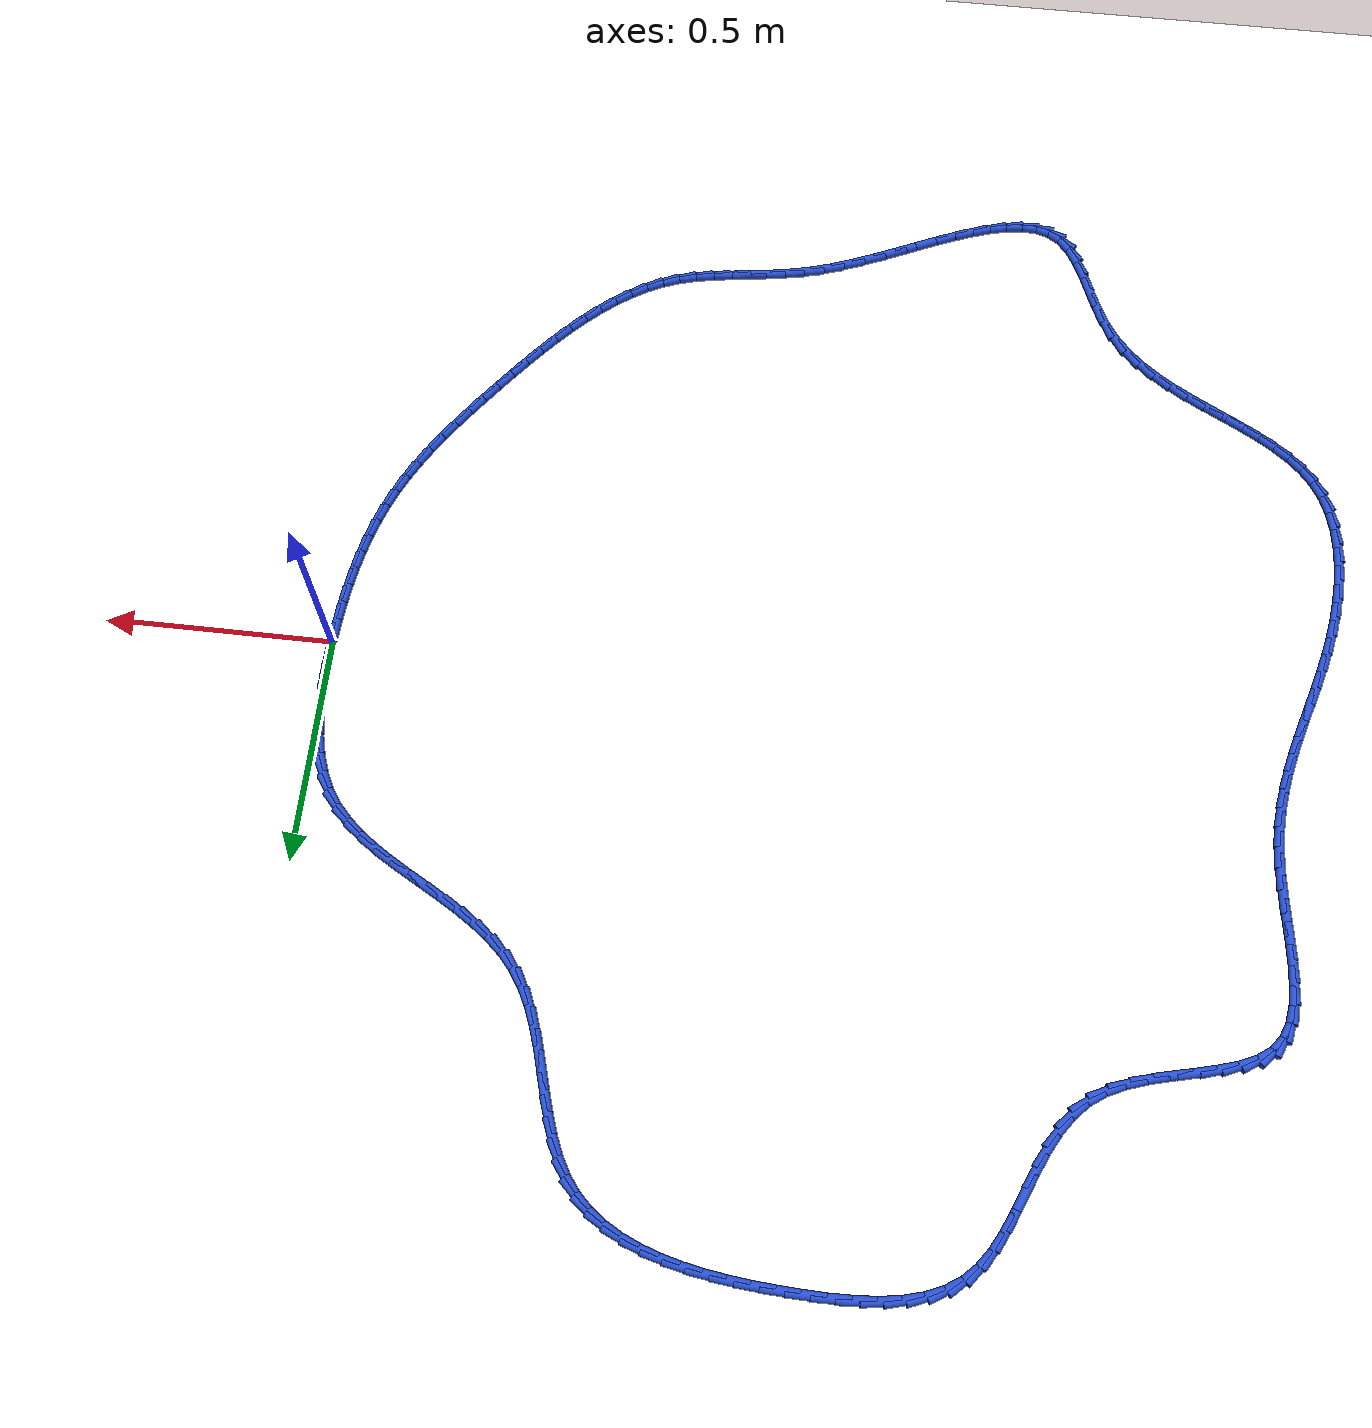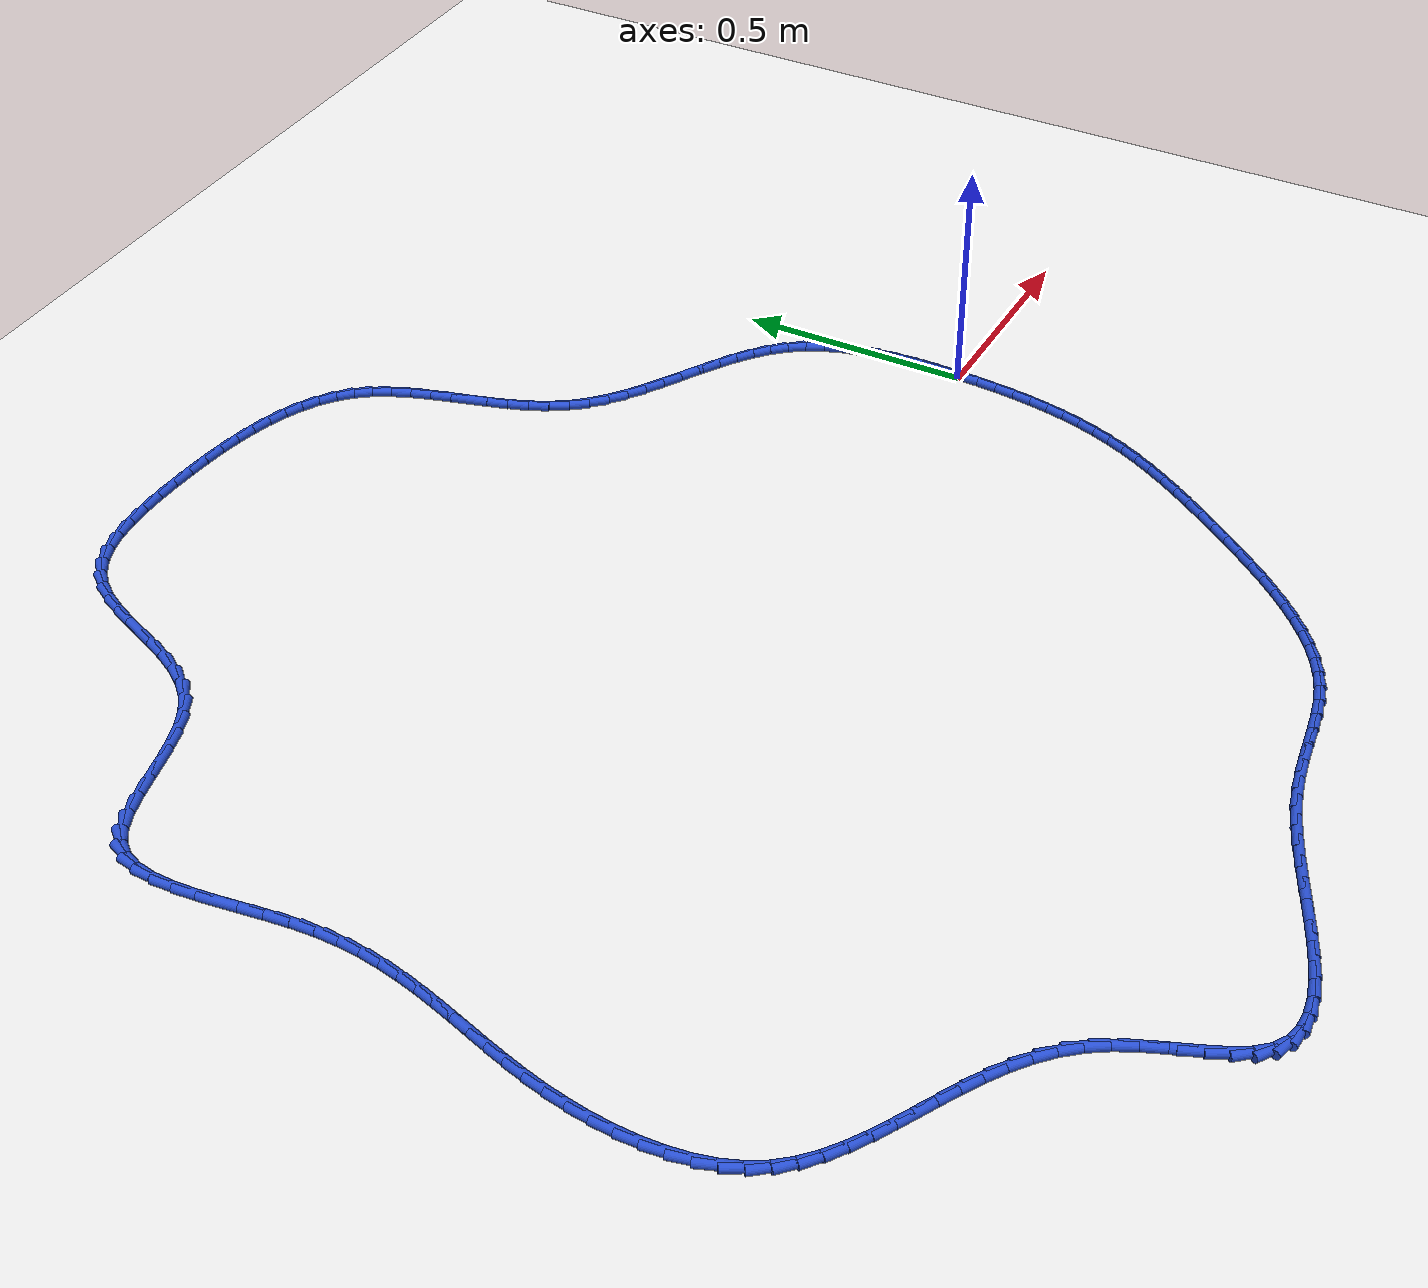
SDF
<sdf version="1.6">
 <world name="default">
  <light name="sun" type="directional">
   <pose>0 0 10 0 -0 0</pose>
   <diffuse>0.8 0.8 0.8 1</diffuse>
   <specular>0.2 0.2 0.2 1</specular>
   <attenuation>
    <range>1000</range>
    <constant>0.9</constant>
    <linear>0.01</linear>
    <quadratic>0.001</quadratic>
   </attenuation>
   <direction>-0.5 0.1 -0.9</direction>
  </light>
  <model name="ground_plane">
   <static>1</static>
   <link name="link">
    <collision name="collision">
     <geometry><plane><normal>0 0 1</normal><size>100 100</size></plane></geometry>
     <surface><friction><ode><mu>100</mu><mu2>50</mu2></ode></friction></surface>
    </collision>
    <visual name="visual">
     <cast_shadows>0</cast_shadows>
     <geometry><plane><normal>0 0 1</normal><size>100 100</size></plane></geometry>
     <material>
      <script><uri>file://media/materials/scripts/gazebo.material</uri><name>Gazebo/WhiteGlow</name></script>
     </material>
    </visual>
   </link>
  </model>
  <gravity>0 0 -9.8</gravity>
  <magnetic_field>6e-06 2.3e-05 -4.2e-05</magnetic_field>
  <atmosphere type="adiabatic"/>
  <physics name="default_physics" default="0" type="ode">
   <max_step_size>0.001</max_step_size>
   <real_time_factor>1</real_time_factor>
   <real_time_update_rate>1000</real_time_update_rate>
  </physics>
  <scene><ambient>0.4 0.4 0.4 1</ambient><background>0.7 0.7 0.7 1</background><shadows>1</shadows></scene>
  <spherical_coordinates>
   <surface_model>EARTH_WGS84</surface_model>
   <latitude_deg>0</latitude_deg>
   <longitude_deg>0</longitude_deg>
   <elevation>0</elevation>
   <heading_deg>0</heading_deg>
  </spherical_coordinates>
  <model name="line">
   <link name="link_0">
    <pose>8.673617379884035e-18 -1.3877787807814457e-17 0.01 0 1.57 1.5404411804849696</pose>
    <collision name="collision">
     <geometry><cylinder><radius>0.01</radius><length>0.08</length></cylinder></geometry>
    </collision>
    <visual name="visual">
     <material>
      <script><name>Gazebo/Blue</name><uri>file://media/materials/scripts/gazebo.material</uri></script>
     </material>
     <geometry><cylinder><radius>0.01</radius><length>0.08</length></cylinder></geometry>
    </visual>
   </link>
   <link name="link_1">
    <pose>0.0013845153484845739 0.04559655424830299 0.01 0 1.57 -1.569472624652564</pose>
    <collision name="collision">
     <geometry><cylinder><radius>0.01</radius><length>0.08</length></cylinder></geometry>
    </collision>
    <visual name="visual">
     <material>
      <script><name>Gazebo/Blue</name><uri>file://media/materials/scripts/gazebo.material</uri></script>
     </material>
     <geometry><cylinder><radius>0.01</radius><length>0.08</length></cylinder></geometry>
    </visual>
   </link>
   <link name="link_2">
    <pose>0.0013239313605063591 0.09136512306441143 0.01 0 1.57 -1.527564902046161</pose>
    <collision name="collision">
     <geometry><cylinder><radius>0.01</radius><length>0.08</length></cylinder></geometry>
    </collision>
    <visual name="visual">
     <material>
      <script><name>Gazebo/Blue</name><uri>file://media/materials/scripts/gazebo.material</uri></script>
     </material>
     <geometry><cylinder><radius>0.01</radius><length>0.08</length></cylinder></geometry>
    </visual>
   </link>
   <link name="link_3">
    <pose>-0.0006421725845916727 0.13681537019135273 0.01 0 1.57 -1.4740586697944864</pose>
    <collision name="collision">
     <geometry><cylinder><radius>0.01</radius><length>0.08</length></cylinder></geometry>
    </collision>
    <visual name="visual">
     <material>
      <script><name>Gazebo/Blue</name><uri>file://media/materials/scripts/gazebo.material</uri></script>
     </material>
     <geometry><cylinder><radius>0.01</radius><length>0.08</length></cylinder></geometry>
    </visual>
   </link>
   <link name="link_4">
    <pose>-0.004974217107466558 0.1814569593721543 0.01 0 1.57 -1.4071152386686927</pose>
    <collision name="collision">
     <geometry><cylinder><radius>0.01</radius><length>0.08</length></cylinder></geometry>
    </collision>
    <visual name="visual">
     <material>
      <script><name>Gazebo/Blue</name><uri>file://media/materials/scripts/gazebo.material</uri></script>
     </material>
     <geometry><cylinder><radius>0.01</radius><length>0.08</length></cylinder></geometry>
    </visual>
   </link>
   <link name="link_5">
    <pose>-0.012132622828775332 0.2247995543498436 0.01 0 1.57 -1.3245299484104283</pose>
    <collision name="collision">
     <geometry><cylinder><radius>0.01</radius><length>0.08</length></cylinder></geometry>
    </collision>
    <visual name="visual">
     <material>
      <script><name>Gazebo/Blue</name><uri>file://media/materials/scripts/gazebo.material</uri></script>
     </material>
     <geometry><cylinder><radius>0.01</radius><length>0.08</length></cylinder></geometry>
    </visual>
   </link>
   <link name="link_6">
    <pose>-0.02257781036917503 0.26635281886744805 0.01 0 1.57 -1.2240264317761655</pose>
    <collision name="collision">
     <geometry><cylinder><radius>0.01</radius><length>0.08</length></cylinder></geometry>
    </collision>
    <visual name="visual">
     <material>
      <script><name>Gazebo/Blue</name><uri>file://media/materials/scripts/gazebo.material</uri></script>
     </material>
     <geometry><cylinder><radius>0.01</radius><length>0.08</length></cylinder></geometry>
    </visual>
   </link>
   <link name="link_7">
    <pose>-0.03677020034932268 0.30562641666799495 0.01 0 1.57 -1.1039057543658062</pose>
    <collision name="collision">
     <geometry><cylinder><radius>0.01</radius><length>0.08</length></cylinder></geometry>
    </collision>
    <visual name="visual">
     <material>
      <script><name>Gazebo/Blue</name><uri>file://media/materials/scripts/gazebo.material</uri></script>
     </material>
     <geometry><cylinder><radius>0.01</radius><length>0.08</length></cylinder></geometry>
    </visual>
   </link>
   <link name="link_8">
    <pose>-0.055170213389875336 0.3421300114945119 0.01 0 1.57 -0.964722960650036</pose>
    <collision name="collision">
     <geometry><cylinder><radius>0.01</radius><length>0.08</length></cylinder></geometry>
    </collision>
    <visual name="visual">
     <material>
      <script><name>Gazebo/Blue</name><uri>file://media/materials/scripts/gazebo.material</uri></script>
     </material>
     <geometry><cylinder><radius>0.01</radius><length>0.08</length></cylinder></geometry>
    </visual>
   </link>
   <link name="link_9">
    <pose>-0.07822112282450329 0.3753881838397205 0.01 0 1.57 -0.8269981324964049</pose>
    <collision name="collision">
     <geometry><cylinder><radius>0.01</radius><length>0.08</length></cylinder></geometry>
    </collision>
    <visual name="visual">
     <material>
      <script><name>Gazebo/Blue</name><uri>file://media/materials/scripts/gazebo.material</uri></script>
     </material>
     <geometry><cylinder><radius>0.01</radius><length>0.08</length></cylinder></geometry>
    </visual>
   </link>
   <link name="link_10">
    <pose>-0.10582831341240703 0.40539343365409924 0.01 0 1.57 -0.7149939350651064</pose>
    <collision name="collision">
     <geometry><cylinder><radius>0.01</radius><length>0.08</length></cylinder></geometry>
    </collision>
    <visual name="visual">
     <material>
      <script><name>Gazebo/Blue</name><uri>file://media/materials/scripts/gazebo.material</uri></script>
     </material>
     <geometry><cylinder><radius>0.01</radius><length>0.08</length></cylinder></geometry>
    </visual>
   </link>
   <link name="link_11">
    <pose>-0.13726492756092257 0.43268826048376147 0.01 0 1.57 -0.6300325433599481</pose>
    <collision name="collision">
     <geometry><cylinder><radius>0.01</radius><length>0.08</length></cylinder></geometry>
    </collision>
    <visual name="visual">
     <material>
      <script><name>Gazebo/Blue</name><uri>file://media/materials/scripts/gazebo.material</uri></script>
     </material>
     <geometry><cylinder><radius>0.01</radius><length>0.08</length></cylinder></geometry>
    </visual>
   </link>
   <link name="link_12">
    <pose>-0.17176793497721776 0.45784663119175517 0.01 0 1.57 -0.5700800207753692</pose>
    <collision name="collision">
     <geometry><cylinder><radius>0.01</radius><length>0.08</length></cylinder></geometry>
    </collision>
    <visual name="visual">
     <material>
      <script><name>Gazebo/Blue</name><uri>file://media/materials/scripts/gazebo.material</uri></script>
     </material>
     <geometry><cylinder><radius>0.01</radius><length>0.08</length></cylinder></geometry>
    </visual>
   </link>
   <link name="link_13">
    <pose>-0.2085743053684603 0.4814425126411283 0.01 0 1.57 -0.5327014073835895</pose>
    <collision name="collision">
     <geometry><cylinder><radius>0.01</radius><length>0.08</length></cylinder></geometry>
    </collision>
    <visual name="visual">
     <material>
      <script><name>Gazebo/Blue</name><uri>file://media/materials/scripts/gazebo.material</uri></script>
     </material>
     <geometry><cylinder><radius>0.01</radius><length>0.08</length></cylinder></geometry>
    </visual>
   </link>
   <link name="link_14">
    <pose>-0.24692100844181802 0.5040498716949288 0.01 0 1.57 -0.5159848641186257</pose>
    <collision name="collision">
     <geometry><cylinder><radius>0.01</radius><length>0.08</length></cylinder></geometry>
    </collision>
    <visual name="visual">
     <material>
      <script><name>Gazebo/Blue</name><uri>file://media/materials/scripts/gazebo.material</uri></script>
     </material>
     <geometry><cylinder><radius>0.01</radius><length>0.08</length></cylinder></geometry>
    </visual>
   </link>
   <link name="link_15">
    <pose>-0.2860450139044586 0.5262426752162045 0.01 0 1.57 -0.5189050249102899</pose>
    <collision name="collision">
     <geometry><cylinder><radius>0.01</radius><length>0.08</length></cylinder></geometry>
    </collision>
    <visual name="visual">
     <material>
      <script><name>Gazebo/Blue</name><uri>file://media/materials/scripts/gazebo.material</uri></script>
     </material>
     <geometry><cylinder><radius>0.01</radius><length>0.08</length></cylinder></geometry>
    </visual>
   </link>
   <link name="link_16">
    <pose>-0.32518329146354996 0.5485948900680037 0.01 0 1.57 -0.5414126193655295</pose>
    <collision name="collision">
     <geometry><cylinder><radius>0.01</radius><length>0.08</length></cylinder></geometry>
    </collision>
    <visual name="visual">
     <material>
      <script><name>Gazebo/Blue</name><uri>file://media/materials/scripts/gazebo.material</uri></script>
     </material>
     <geometry><cylinder><radius>0.01</radius><length>0.08</length></cylinder></geometry>
    </visual>
   </link>
   <link name="link_17">
    <pose>-0.3635728108262599 0.571680483113374 0.01 0 1.57 -0.5843854394884281</pose>
    <collision name="collision">
     <geometry><cylinder><radius>0.01</radius><length>0.08</length></cylinder></geometry>
    </collision>
    <visual name="visual">
     <material>
      <script><name>Gazebo/Blue</name><uri>file://media/materials/scripts/gazebo.material</uri></script>
     </material>
     <geometry><cylinder><radius>0.01</radius><length>0.08</length></cylinder></geometry>
    </visual>
   </link>
   <link name="link_18">
    <pose>-0.40045054169975586 0.5960734212153636 0.01 0 1.57 -0.6494313331032872</pose>
    <collision name="collision">
     <geometry><cylinder><radius>0.01</radius><length>0.08</length></cylinder></geometry>
    </collision>
    <visual name="visual">
     <material>
      <script><name>Gazebo/Blue</name><uri>file://media/materials/scripts/gazebo.material</uri></script>
     </material>
     <geometry><cylinder><radius>0.01</radius><length>0.08</length></cylinder></geometry>
    </visual>
   </link>
   <link name="link_19">
    <pose>-0.435053453791206 0.6223476712370204 0.01 0 1.57 -0.7384047845697882</pose>
    <collision name="collision">
     <geometry><cylinder><radius>0.01</radius><length>0.08</length></cylinder></geometry>
    </collision>
    <visual name="visual">
     <material>
      <script><name>Gazebo/Blue</name><uri>file://media/materials/scripts/gazebo.material</uri></script>
     </material>
     <geometry><cylinder><radius>0.01</radius><length>0.08</length></cylinder></geometry>
    </visual>
   </link>
   <link name="link_20">
    <pose>-0.466618516807778 0.6510772000413922 0.01 0 1.57 -0.8524077708560719</pose>
    <collision name="collision">
     <geometry><cylinder><radius>0.01</radius><length>0.08</length></cylinder></geometry>
    </collision>
    <visual name="visual">
     <material>
      <script><name>Gazebo/Blue</name><uri>file://media/materials/scripts/gazebo.material</uri></script>
     </material>
     <geometry><cylinder><radius>0.01</radius><length>0.08</length></cylinder></geometry>
    </visual>
   </link>
   <link name="link_21">
    <pose>-0.4943827004566395 0.6828359744915273 0.01 0 1.57 -0.9862905099047623</pose>
    <collision name="collision">
     <geometry><cylinder><radius>0.01</radius><length>0.08</length></cylinder></geometry>
    </collision>
    <visual name="visual">
     <material>
      <script><name>Gazebo/Blue</name><uri>file://media/materials/scripts/gazebo.material</uri></script>
     </material>
     <geometry><cylinder><radius>0.01</radius><length>0.08</length></cylinder></geometry>
    </visual>
   </link>
   <link name="link_22">
    <pose>-0.5177106823630979 0.7180944585080532 0.01 0 1.57 -1.1051406171056437</pose>
    <collision name="collision">
     <geometry><cylinder><radius>0.01</radius><length>0.08</length></cylinder></geometry>
    </collision>
    <visual name="visual">
     <material>
      <script><name>Gazebo/Blue</name><uri>file://media/materials/scripts/gazebo.material</uri></script>
     </material>
     <geometry><cylinder><radius>0.01</radius><length>0.08</length></cylinder></geometry>
    </visual>
   </link>
   <link name="link_23">
    <pose>-0.5370020797606627 0.756484332510644 0.01 0 1.57 -1.1932959229504543</pose>
    <collision name="collision">
     <geometry><cylinder><radius>0.01</radius><length>0.08</length></cylinder></geometry>
    </collision>
    <visual name="visual">
     <material>
      <script><name>Gazebo/Blue</name><uri>file://media/materials/scripts/gazebo.material</uri></script>
     </material>
     <geometry><cylinder><radius>0.01</radius><length>0.08</length></cylinder></geometry>
    </visual>
   </link>
   <link name="link_24">
    <pose>-0.5531585836852521 0.7972303631064355 0.01 0 1.57 -1.2529096891502483</pose>
    <collision name="collision">
     <geometry><cylinder><radius>0.01</radius><length>0.08</length></cylinder></geometry>
    </collision>
    <visual name="visual">
     <material>
      <script><name>Gazebo/Blue</name><uri>file://media/materials/scripts/gazebo.material</uri></script>
     </material>
     <geometry><cylinder><radius>0.01</radius><length>0.08</length></cylinder></geometry>
    </visual>
   </link>
   <link name="link_25">
    <pose>-0.5670851978884233 0.8395546320587337 0.01 0 1.57 -1.2864953150644989</pose>
    <collision name="collision">
     <geometry><cylinder><radius>0.01</radius><length>0.08</length></cylinder></geometry>
    </collision>
    <visual name="visual">
     <material>
      <script><name>Gazebo/Blue</name><uri>file://media/materials/scripts/gazebo.material</uri></script>
     </material>
     <geometry><cylinder><radius>0.01</radius><length>0.08</length></cylinder></geometry>
    </visual>
   </link>
   <link name="link_26">
    <pose>-0.5796869261217332 0.8826792211308442 0.01 0 1.57 -1.2956249751863824</pose>
    <collision name="collision">
     <geometry><cylinder><radius>0.01</radius><length>0.08</length></cylinder></geometry>
    </collision>
    <visual name="visual">
     <material>
      <script><name>Gazebo/Blue</name><uri>file://media/materials/scripts/gazebo.material</uri></script>
     </material>
     <geometry><cylinder><radius>0.01</radius><length>0.08</length></cylinder></geometry>
    </visual>
   </link>
   <link name="link_27">
    <pose>-0.5918687721367395 0.9258262120860725 0.01 0 1.57 -1.2804322602272586</pose>
    <collision name="collision">
     <geometry><cylinder><radius>0.01</radius><length>0.08</length></cylinder></geometry>
    </collision>
    <visual name="visual">
     <material>
      <script><name>Gazebo/Blue</name><uri>file://media/materials/scripts/gazebo.material</uri></script>
     </material>
     <geometry><cylinder><radius>0.01</radius><length>0.08</length></cylinder></geometry>
    </visual>
   </link>
   <link name="link_28">
    <pose>-0.604535739684999 0.968217686687725 0.01 0 1.57 -1.2394345128430861</pose>
    <collision name="collision">
     <geometry><cylinder><radius>0.01</radius><length>0.08</length></cylinder></geometry>
    </collision>
    <visual name="visual">
     <material>
      <script><name>Gazebo/Blue</name><uri>file://media/materials/scripts/gazebo.material</uri></script>
     </material>
     <geometry><cylinder><radius>0.01</radius><length>0.08</length></cylinder></geometry>
    </visual>
   </link>
   <link name="link_29">
    <pose>-0.6185928325180692 1.009075726699107 0.01 0 1.57 -1.1695877139725752</pose>
    <collision name="collision">
     <geometry><cylinder><radius>0.01</radius><length>0.08</length></cylinder></geometry>
    </collision>
    <visual name="visual">
     <material>
      <script><name>Gazebo/Blue</name><uri>file://media/materials/scripts/gazebo.material</uri></script>
     </material>
     <geometry><cylinder><radius>0.01</radius><length>0.08</length></cylinder></geometry>
    </visual>
   </link>
   <link name="link_30">
    <pose>-0.6349450543875073 1.0476224138835246 0.01 0 1.57 -1.0668543398511647</pose>
    <collision name="collision">
     <geometry><cylinder><radius>0.01</radius><length>0.08</length></cylinder></geometry>
    </collision>
    <visual name="visual">
     <material>
      <script><name>Gazebo/Blue</name><uri>file://media/materials/scripts/gazebo.material</uri></script>
     </material>
     <geometry><cylinder><radius>0.01</radius><length>0.08</length></cylinder></geometry>
    </visual>
   </link>
   <link name="link_31">
    <pose>-0.65449740904487 1.0830798300042832 0.01 0 1.57 -0.9286748813449177</pose>
    <collision name="collision">
     <geometry><cylinder><radius>0.01</radius><length>0.08</length></cylinder></geometry>
    </collision>
    <visual name="visual">
     <material>
      <script><name>Gazebo/Blue</name><uri>file://media/materials/scripts/gazebo.material</uri></script>
     </material>
     <geometry><cylinder><radius>0.01</radius><length>0.08</length></cylinder></geometry>
    </visual>
   </link>
   <link name="link_32">
    <pose>-0.6781344609064812 1.1146866527510004 0.01 0 1.57 -0.7758209641705359</pose>
    <collision name="collision">
     <geometry><cylinder><radius>0.01</radius><length>0.08</length></cylinder></geometry>
    </collision>
    <visual name="visual">
     <material>
      <script><name>Gazebo/Blue</name><uri>file://media/materials/scripts/gazebo.material</uri></script>
     </material>
     <geometry><cylinder><radius>0.01</radius><length>0.08</length></cylinder></geometry>
    </visual>
   </link>
   <link name="link_33">
    <pose>-0.7061447571134276 1.1421655021072694 0.01 0 1.57 -0.6359548162598948</pose>
    <collision name="collision">
     <geometry><cylinder><radius>0.01</radius><length>0.08</length></cylinder></geometry>
    </collision>
    <visual name="visual">
     <material>
      <script><name>Gazebo/Blue</name><uri>file://media/materials/scripts/gazebo.material</uri></script>
     </material>
     <geometry><cylinder><radius>0.01</radius><length>0.08</length></cylinder></geometry>
    </visual>
   </link>
   <link name="link_34">
    <pose>-0.7381411464522578 1.165787638214132 0.01 0 1.57 -0.5137644723700223</pose>
    <collision name="collision">
     <geometry><cylinder><radius>0.01</radius><length>0.08</length></cylinder></geometry>
    </collision>
    <visual name="visual">
     <material>
      <script><name>Gazebo/Blue</name><uri>file://media/materials/scripts/gazebo.material</uri></script>
     </material>
     <geometry><cylinder><radius>0.01</radius><length>0.08</length></cylinder></geometry>
    </visual>
   </link>
   <link name="link_35">
    <pose>-0.7737000234628637 1.1858539206093035 0.01 0 1.57 -0.40982685411062253</pose>
    <collision name="collision">
     <geometry><cylinder><radius>0.01</radius><length>0.08</length></cylinder></geometry>
    </collision>
    <visual name="visual">
     <material>
      <script><name>Gazebo/Blue</name><uri>file://media/materials/scripts/gazebo.material</uri></script>
     </material>
     <geometry><cylinder><radius>0.01</radius><length>0.08</length></cylinder></geometry>
    </visual>
   </link>
   <link name="link_36">
    <pose>-0.8123977826851357 1.2026652088304997 0.01 0 1.57 -0.3228977593227513</pose>
    <collision name="collision">
     <geometry><cylinder><radius>0.01</radius><length>0.08</length></cylinder></geometry>
    </collision>
    <visual name="visual">
     <material>
      <script><name>Gazebo/Blue</name><uri>file://media/materials/scripts/gazebo.material</uri></script>
     </material>
     <geometry><cylinder><radius>0.01</radius><length>0.08</length></cylinder></geometry>
    </visual>
   </link>
   <link name="link_37">
    <pose>-0.8538108186589655 1.2165223624154353 0.01 0 1.57 -0.25094994207727717</pose>
    <collision name="collision">
     <geometry><cylinder><radius>0.01</radius><length>0.08</length></cylinder></geometry>
    </collision>
    <visual name="visual">
     <material>
      <script><name>Gazebo/Blue</name><uri>file://media/materials/scripts/gazebo.material</uri></script>
     </material>
     <geometry><cylinder><radius>0.01</radius><length>0.08</length></cylinder></geometry>
    </visual>
   </link>
   <link name="link_38">
    <pose>-0.8975155259242433 1.2277262409018248 0.01 0 1.57 -0.19183848445173293</pose>
    <collision name="collision">
     <geometry><cylinder><radius>0.01</radius><length>0.08</length></cylinder></geometry>
    </collision>
    <visual name="visual">
     <material>
      <script><name>Gazebo/Blue</name><uri>file://media/materials/scripts/gazebo.material</uri></script>
     </material>
     <geometry><cylinder><radius>0.01</radius><length>0.08</length></cylinder></geometry>
    </visual>
   </link>
   <link name="link_39">
    <pose>-0.9430882990208614 1.2365777038273842 0.01 0 1.57 -0.14362994734283263</pose>
    <collision name="collision">
     <geometry><cylinder><radius>0.01</radius><length>0.08</length></cylinder></geometry>
    </collision>
    <visual name="visual">
     <material>
      <script><name>Gazebo/Blue</name><uri>file://media/materials/scripts/gazebo.material</uri></script>
     </material>
     <geometry><cylinder><radius>0.01</radius><length>0.08</length></cylinder></geometry>
    </visual>
   </link>
   <link name="link_40">
    <pose>-0.9901055324887096 1.2433776107298278 0.01 0 1.57 -0.10472395276142259</pose>
    <collision name="collision">
     <geometry><cylinder><radius>0.01</radius><length>0.08</length></cylinder></geometry>
    </collision>
    <visual name="visual">
     <material>
      <script><name>Gazebo/Blue</name><uri>file://media/materials/scripts/gazebo.material</uri></script>
     </material>
     <geometry><cylinder><radius>0.01</radius><length>0.08</length></cylinder></geometry>
    </visual>
   </link>
   <link name="link_41">
    <pose>-1.03814362086768 1.2484268211468712 0.01 0 1.57 -0.07387269782615163</pose>
    <collision name="collision">
     <geometry><cylinder><radius>0.01</radius><length>0.08</length></cylinder></geometry>
    </collision>
    <visual name="visual">
     <material>
      <script><name>Gazebo/Blue</name><uri>file://media/materials/scripts/gazebo.material</uri></script>
     </material>
     <geometry><cylinder><radius>0.01</radius><length>0.08</length></cylinder></geometry>
    </visual>
   </link>
   <link name="link_42">
    <pose>-1.0867789586976624 1.2520261946162285 0.01 0 1.57 -0.04993034661588256</pose>
    <collision name="collision">
     <geometry><cylinder><radius>0.01</radius><length>0.08</length></cylinder></geometry>
    </collision>
    <visual name="visual">
     <material>
      <script><name>Gazebo/Blue</name><uri>file://media/materials/scripts/gazebo.material</uri></script>
     </material>
     <geometry><cylinder><radius>0.01</radius><length>0.08</length></cylinder></geometry>
    </visual>
   </link>
   <link name="link_43">
    <pose>-1.1355854543903534 1.254465147001767 0.01 0 1.57 -0.023673149301641903</pose>
    <collision name="collision">
     <geometry><cylinder><radius>0.01</radius><length>0.08</length></cylinder></geometry>
    </collision>
    <visual name="visual">
     <material>
      <script><name>Gazebo/Blue</name><uri>file://media/materials/scripts/gazebo.material</uri></script>
     </material>
     <geometry><cylinder><radius>0.01</radius><length>0.08</length></cylinder></geometry>
    </visual>
   </link>
   <link name="link_44">
    <pose>-1.1840456571895621 1.255612566970763 0.01 0 1.57 0.01701203568731349</pose>
    <collision name="collision">
     <geometry><cylinder><radius>0.01</radius><length>0.08</length></cylinder></geometry>
    </collision>
    <visual name="visual">
     <material>
      <script><name>Gazebo/Blue</name><uri>file://media/materials/scripts/gazebo.material</uri></script>
     </material>
     <geometry><cylinder><radius>0.01</radius><length>0.08</length></cylinder></geometry>
    </visual>
   </link>
   <link name="link_45">
    <pose>-1.2315264097976346 1.2548047447809965 0.01 0 1.57 0.07532541561170775</pose>
    <collision name="collision">
     <geometry><cylinder><radius>0.01</radius><length>0.08</length></cylinder></geometry>
    </collision>
    <visual name="visual">
     <material>
      <script><name>Gazebo/Blue</name><uri>file://media/materials/scripts/gazebo.material</uri></script>
     </material>
     <geometry><cylinder><radius>0.01</radius><length>0.08</length></cylinder></geometry>
    </visual>
   </link>
   <link name="link_46">
    <pose>-1.2773871139506765 1.2513437198455402 0.01 0 1.57 0.15498956158423655</pose>
    <collision name="collision">
     <geometry><cylinder><radius>0.01</radius><length>0.08</length></cylinder></geometry>
    </collision>
    <visual name="visual">
     <material>
      <script><name>Gazebo/Blue</name><uri>file://media/materials/scripts/gazebo.material</uri></script>
     </material>
     <geometry><cylinder><radius>0.01</radius><length>0.08</length></cylinder></geometry>
    </visual>
   </link>
   <link name="link_47">
    <pose>-1.320987171384797 1.2445315315774677 0.01 0 1.57 0.26079267739791234</pose>
    <collision name="collision">
     <geometry><cylinder><radius>0.01</radius><length>0.08</length></cylinder></geometry>
    </collision>
    <visual name="visual">
     <material>
      <script><name>Gazebo/Blue</name><uri>file://media/materials/scripts/gazebo.material</uri></script>
     </material>
     <geometry><cylinder><radius>0.01</radius><length>0.08</length></cylinder></geometry>
    </visual>
   </link>
   <link name="link_48">
    <pose>-1.3616859838361028 1.233670219389853 0.01 0 1.57 0.39768448859703687</pose>
    <collision name="collision">
     <geometry><cylinder><radius>0.01</radius><length>0.08</length></cylinder></geometry>
    </collision>
    <visual name="visual">
     <material>
      <script><name>Gazebo/Blue</name><uri>file://media/materials/scripts/gazebo.material</uri></script>
     </material>
     <geometry><cylinder><radius>0.01</radius><length>0.08</length></cylinder></geometry>
    </visual>
   </link>
   <link name="link_49">
    <pose>-1.3988429530407014 1.2180618226957685 0.01 0 1.57 0.568231225746723</pose>
    <collision name="collision">
     <geometry><cylinder><radius>0.01</radius><length>0.08</length></cylinder></geometry>
    </collision>
    <visual name="visual">
     <material>
      <script><name>Gazebo/Blue</name><uri>file://media/materials/scripts/gazebo.material</uri></script>
     </material>
     <geometry><cylinder><radius>0.01</radius><length>0.08</length></cylinder></geometry>
    </visual>
   </link>
   <link name="link_50">
    <pose>-1.4318174807347015 1.1970083809082874 0.01 0 1.57 0.7651334246916499</pose>
    <collision name="collision">
     <geometry><cylinder><radius>0.01</radius><length>0.08</length></cylinder></geometry>
    </collision>
    <visual name="visual">
     <material>
      <script><name>Gazebo/Blue</name><uri>file://media/materials/scripts/gazebo.material</uri></script>
     </material>
     <geometry><cylinder><radius>0.01</radius><length>0.08</length></cylinder></geometry>
    </visual>
   </link>
   <link name="link_51">
    <pose>-1.460047176693905 1.1699002451794949 0.01 0 1.57 0.9386870698864203</pose>
    <collision name="collision">
     <geometry><cylinder><radius>0.01</radius><length>0.08</length></cylinder></geometry>
    </collision>
    <visual name="visual">
     <material>
      <script><name>Gazebo/Blue</name><uri>file://media/materials/scripts/gazebo.material</uri></script>
     </material>
     <geometry><cylinder><radius>0.01</radius><length>0.08</length></cylinder></geometry>
    </visual>
   </link>
   <link name="link_52">
    <pose>-1.4839608092331609 1.1372469730059778 0.01 0 1.57 1.059655129121919</pose>
    <collision name="collision">
     <geometry><cylinder><radius>0.01</radius><length>0.08</length></cylinder></geometry>
    </collision>
    <visual name="visual">
     <material>
      <script><name>Gazebo/Blue</name><uri>file://media/materials/scripts/gazebo.material</uri></script>
     </material>
     <geometry><cylinder><radius>0.01</radius><length>0.08</length></cylinder></geometry>
    </visual>
   </link>
   <link name="link_53">
    <pose>-1.5046678197249408 1.1003267311174731 0.01 0 1.57 1.1340458390978203</pose>
    <collision name="collision">
     <geometry><cylinder><radius>0.01</radius><length>0.08</length></cylinder></geometry>
    </collision>
    <visual name="visual">
     <material>
      <script><name>Gazebo/Blue</name><uri>file://media/materials/scripts/gazebo.material</uri></script>
     </material>
     <geometry><cylinder><radius>0.01</radius><length>0.08</length></cylinder></geometry>
    </visual>
   </link>
   <link name="link_54">
    <pose>-1.5232909983167524 1.0604327595474556 0.01 0 1.57 1.169068488118103</pose>
    <collision name="collision">
     <geometry><cylinder><radius>0.01</radius><length>0.08</length></cylinder></geometry>
    </collision>
    <visual name="visual">
     <material>
      <script><name>Gazebo/Blue</name><uri>file://media/materials/scripts/gazebo.material</uri></script>
     </material>
     <geometry><cylinder><radius>0.01</radius><length>0.08</length></cylinder></geometry>
    </visual>
   </link>
   <link name="link_55">
    <pose>-1.540953135156104 1.0188582983293986 0.01 0 1.57 1.1691243570447343</pose>
    <collision name="collision">
     <geometry><cylinder><radius>0.01</radius><length>0.08</length></cylinder></geometry>
    </collision>
    <visual name="visual">
     <material>
      <script><name>Gazebo/Blue</name><uri>file://media/materials/scripts/gazebo.material</uri></script>
     </material>
     <geometry><cylinder><radius>0.01</radius><length>0.08</length></cylinder></geometry>
    </visual>
   </link>
   <link name="link_56">
    <pose>-1.5587770203905011 0.9768965874967762 0.01 0 1.57 1.1351879654113437</pose>
    <collision name="collision">
     <geometry><cylinder><radius>0.01</radius><length>0.08</length></cylinder></geometry>
    </collision>
    <visual name="visual">
     <material>
      <script><name>Gazebo/Blue</name><uri>file://media/materials/scripts/gazebo.material</uri></script>
     </material>
     <geometry><cylinder><radius>0.01</radius><length>0.08</length></cylinder></geometry>
    </visual>
   </link>
   <link name="link_57">
    <pose>-1.5778854441674524 0.9358408670830636 0.01 0 1.57 1.0650988614510735</pose>
    <collision name="collision">
     <geometry><cylinder><radius>0.01</radius><length>0.08</length></cylinder></geometry>
    </collision>
    <visual name="visual">
     <material>
      <script><name>Gazebo/Blue</name><uri>file://media/materials/scripts/gazebo.material</uri></script>
     </material>
     <geometry><cylinder><radius>0.01</radius><length>0.08</length></cylinder></geometry>
    </visual>
   </link>
   <link name="link_58">
    <pose>-1.599401196634465 0.8969843771217336 0.01 0 1.57 0.9545679799490933</pose>
    <collision name="collision">
     <geometry><cylinder><radius>0.01</radius><length>0.08</length></cylinder></geometry>
    </collision>
    <visual name="visual">
     <material>
      <script><name>Gazebo/Blue</name><uri>file://media/materials/scripts/gazebo.material</uri></script>
     </material>
     <geometry><cylinder><radius>0.01</radius><length>0.08</length></cylinder></geometry>
    </visual>
   </link>
   <link name="link_59">
    <pose>-1.624447067939046 0.8616203576462618 0.01 0 1.57 0.7999885536335777</pose>
    <collision name="collision">
     <geometry><cylinder><radius>0.01</radius><length>0.08</length></cylinder></geometry>
    </collision>
    <visual name="visual">
     <material>
      <script><name>Gazebo/Blue</name><uri>file://media/materials/scripts/gazebo.material</uri></script>
     </material>
     <geometry><cylinder><radius>0.01</radius><length>0.08</length></cylinder></geometry>
    </visual>
   </link>
   <link name="link_60">
    <pose>-1.6541458482287026 0.8310420486901213 0.01 0 1.57 0.607718900748891</pose>
    <collision name="collision">
     <geometry><cylinder><radius>0.01</radius><length>0.08</length></cylinder></geometry>
    </collision>
    <visual name="visual">
     <material>
      <script><name>Gazebo/Blue</name><uri>file://media/materials/scripts/gazebo.material</uri></script>
     </material>
     <geometry><cylinder><radius>0.01</radius><length>0.08</length></cylinder></geometry>
    </visual>
   </link>
   <link name="link_61">
    <pose>-1.6895166786201428 0.8064406148847577 0.01 0 1.57 0.4369143367108485</pose>
    <collision name="collision">
     <geometry><cylinder><radius>0.01</radius><length>0.08</length></cylinder></geometry>
    </collision>
    <visual name="visual">
     <material>
      <script><name>Gazebo/Blue</name><uri>file://media/materials/scripts/gazebo.material</uri></script>
     </material>
     <geometry><cylinder><radius>0.01</radius><length>0.08</length></cylinder></geometry>
    </visual>
   </link>
   <link name="link_62">
    <pose>-1.7300563078834523 0.7875079419042743 0.01 0 1.57 0.32235186396065074</pose>
    <collision name="collision">
     <geometry><cylinder><radius>0.01</radius><length>0.08</length></cylinder></geometry>
    </collision>
    <visual name="visual">
     <material>
      <script><name>Gazebo/Blue</name><uri>file://media/materials/scripts/gazebo.material</uri></script>
     </material>
     <geometry><cylinder><radius>0.01</radius><length>0.08</length></cylinder></geometry>
    </visual>
   </link>
   <link name="link_63">
    <pose>-1.7741039536307657 0.7727959582287991 0.01 0 1.57 0.25524072422625366</pose>
    <collision name="collision">
     <geometry><cylinder><radius>0.01</radius><length>0.08</length></cylinder></geometry>
    </collision>
    <visual name="visual">
     <material>
      <script><name>Gazebo/Blue</name><uri>file://media/materials/scripts/gazebo.material</uri></script>
     </material>
     <geometry><cylinder><radius>0.01</radius><length>0.08</length></cylinder></geometry>
    </visual>
   </link>
   <link name="link_64">
    <pose>-1.8199698782892837 0.7608280767592978 0.01 0 1.57 0.22857870780461786</pose>
    <collision name="collision">
     <geometry><cylinder><radius>0.01</radius><length>0.08</length></cylinder></geometry>
    </collision>
    <visual name="visual">
     <material>
      <script><name>Gazebo/Blue</name><uri>file://media/materials/scripts/gazebo.material</uri></script>
     </material>
     <geometry><cylinder><radius>0.01</radius><length>0.08</length></cylinder></geometry>
    </visual>
   </link>
   <link name="link_65">
    <pose>-1.8659643442862077 0.7501277103967352 0.01 0 1.57 0.2407616306191169</pose>
    <collision name="collision">
     <geometry><cylinder><radius>0.01</radius><length>0.08</length></cylinder></geometry>
    </collision>
    <visual name="visual">
     <material>
      <script><name>Gazebo/Blue</name><uri>file://media/materials/scripts/gazebo.material</uri></script>
     </material>
     <geometry><cylinder><radius>0.01</radius><length>0.08</length></cylinder></geometry>
    </visual>
   </link>
   <link name="link_66">
    <pose>-1.9103976140487386 0.7392182720420767 0.01 0 1.57 0.2968035414182749</pose>
    <collision name="collision">
     <geometry><cylinder><radius>0.01</radius><length>0.08</length></cylinder></geometry>
    </collision>
    <visual name="visual">
     <material>
      <script><name>Gazebo/Blue</name><uri>file://media/materials/scripts/gazebo.material</uri></script>
     </material>
     <geometry><cylinder><radius>0.01</radius><length>0.08</length></cylinder></geometry>
    </visual>
   </link>
   <link name="link_67">
    <pose>-1.9515799500040765 0.7266231745962871 0.01 0 1.57 0.4101296186176226</pose>
    <collision name="collision">
     <geometry><cylinder><radius>0.01</radius><length>0.08</length></cylinder></geometry>
    </collision>
    <visual name="visual">
     <material>
      <script><name>Gazebo/Blue</name><uri>file://media/materials/scripts/gazebo.material</uri></script>
     </material>
     <geometry><cylinder><radius>0.01</radius><length>0.08</length></cylinder></geometry>
    </visual>
   </link>
   <link name="link_68">
    <pose>-1.9878216145794225 0.7108658309603315 0.01 0 1.57 0.603168287672965</pose>
    <collision name="collision">
     <geometry><cylinder><radius>0.01</radius><length>0.08</length></cylinder></geometry>
    </collision>
    <visual name="visual">
     <material>
      <script><name>Gazebo/Blue</name><uri>file://media/materials/scripts/gazebo.material</uri></script>
     </material>
     <geometry><cylinder><radius>0.01</radius><length>0.08</length></cylinder></geometry>
    </visual>
   </link>
   <link name="link_69">
    <pose>-2.0174328702019775 0.6904696540351757 0.01 0 1.57 0.8889663896637061</pose>
    <collision name="collision">
     <geometry><cylinder><radius>0.01</radius><length>0.08</length></cylinder></geometry>
    </collision>
    <visual name="visual">
     <material>
      <script><name>Gazebo/Blue</name><uri>file://media/materials/scripts/gazebo.material</uri></script>
     </material>
     <geometry><cylinder><radius>0.01</radius><length>0.08</length></cylinder></geometry>
    </visual>
   </link>
   <link name="link_70">
    <pose>-2.0388628898275307 0.6640680047141443 0.01 0 1.57 1.1784163692076206</pose>
    <collision name="collision">
     <geometry><cylinder><radius>0.01</radius><length>0.08</length></cylinder></geometry>
    </collision>
    <visual name="visual">
     <material>
      <script><name>Gazebo/Blue</name><uri>file://media/materials/scripts/gazebo.material</uri></script>
     </material>
     <geometry><cylinder><radius>0.01</radius><length>0.08</length></cylinder></geometry>
    </visual>
   </link>
   <link name="link_71">
    <pose>-2.052277511643157 0.6316529882395371 0.01 0 1.57 1.3934941462807175</pose>
    <collision name="collision">
     <geometry><cylinder><radius>0.01</radius><length>0.08</length></cylinder></geometry>
    </collision>
    <visual name="visual">
     <material>
      <script><name>Gazebo/Blue</name><uri>file://media/materials/scripts/gazebo.material</uri></script>
     </material>
     <geometry><cylinder><radius>0.01</radius><length>0.08</length></cylinder></geometry>
    </visual>
   </link>
   <link name="link_72">
    <pose>-2.0590004523310976 0.5941331732580741 0.01 0 1.57 1.5377938032586311</pose>
    <collision name="collision">
     <geometry><cylinder><radius>0.01</radius><length>0.08</length></cylinder></geometry>
    </collision>
    <visual name="visual">
     <material>
      <script><name>Gazebo/Blue</name><uri>file://media/materials/scripts/gazebo.material</uri></script>
     </material>
     <geometry><cylinder><radius>0.01</radius><length>0.08</length></cylinder></geometry>
    </visual>
   </link>
   <link name="link_73">
    <pose>-2.0603771203039543 0.5524342974693044 0.01 0 1.57 -1.5124850217161692</pose>
    <collision name="collision">
     <geometry><cylinder><radius>0.01</radius><length>0.08</length></cylinder></geometry>
    </collision>
    <visual name="visual">
     <material>
      <script><name>Gazebo/Blue</name><uri>file://media/materials/scripts/gazebo.material</uri></script>
     </material>
     <geometry><cylinder><radius>0.01</radius><length>0.08</length></cylinder></geometry>
    </visual>
   </link>
   <link name="link_74">
    <pose>-2.057752923974331 0.507482098572777 0.01 0 1.57 -1.4595887646121977</pose>
    <collision name="collision">
     <geometry><cylinder><radius>0.01</radius><length>0.08</length></cylinder></geometry>
    </collision>
    <visual name="visual">
     <material>
      <script><name>Gazebo/Blue</name><uri>file://media/materials/scripts/gazebo.material</uri></script>
     </material>
     <geometry><cylinder><radius>0.01</radius><length>0.08</length></cylinder></geometry>
    </visual>
   </link>
   <link name="link_75">
    <pose>-2.0524732717548297 0.4602023142680419 0.01 0 1.57 -1.4362509530597052</pose>
    <collision name="collision">
     <geometry><cylinder><radius>0.01</radius><length>0.08</length></cylinder></geometry>
    </collision>
    <visual name="visual">
     <material>
      <script><name>Gazebo/Blue</name><uri>file://media/materials/scripts/gazebo.material</uri></script>
     </material>
     <geometry><cylinder><radius>0.01</radius><length>0.08</length></cylinder></geometry>
    </visual>
   </link>
   <link name="link_76">
    <pose>-2.045883572058054 0.41152068225464833 0.01 0 1.57 -1.438245330989654</pose>
    <collision name="collision">
     <geometry><cylinder><radius>0.01</radius><length>0.08</length></cylinder></geometry>
    </collision>
    <visual name="visual">
     <material>
      <script><name>Gazebo/Blue</name><uri>file://media/materials/scripts/gazebo.material</uri></script>
     </material>
     <geometry><cylinder><radius>0.01</radius><length>0.08</length></cylinder></geometry>
    </visual>
   </link>
   <link name="link_77">
    <pose>-2.0393292332966073 0.3623629402321451 0.01 0 1.57 -1.4649773185020307</pose>
    <collision name="collision">
     <geometry><cylinder><radius>0.01</radius><length>0.08</length></cylinder></geometry>
    </collision>
    <visual name="visual">
     <material>
      <script><name>Gazebo/Blue</name><uri>file://media/materials/scripts/gazebo.material</uri></script>
     </material>
     <geometry><cylinder><radius>0.01</radius><length>0.08</length></cylinder></geometry>
    </visual>
   </link>
   <link name="link_78">
    <pose>-2.0341556638830904 0.31365482590008226 0.01 0 1.57 -1.5187879900041479</pose>
    <collision name="collision">
     <geometry><cylinder><radius>0.01</radius><length>0.08</length></cylinder></geometry>
    </collision>
    <visual name="visual">
     <material>
      <script><name>Gazebo/Blue</name><uri>file://media/materials/scripts/gazebo.material</uri></script>
     </material>
     <geometry><cylinder><radius>0.01</radius><length>0.08</length></cylinder></geometry>
    </visual>
   </link>
   <link name="link_79">
    <pose>-2.0316911442934686 0.2663105485248813 0.01 0 1.57 1.552027496441594</pose>
    <collision name="collision">
     <geometry><cylinder><radius>0.01</radius><length>0.08</length></cylinder></geometry>
    </collision>
    <visual name="visual">
     <material>
      <script><name>Gazebo/Blue</name><uri>file://media/materials/scripts/gazebo.material</uri></script>
     </material>
     <geometry><cylinder><radius>0.01</radius><length>0.08</length></cylinder></geometry>
    </visual>
   </link>
   <link name="link_80">
    <pose>-2.032546153048206 0.22076118084474972 0.01 0 1.57 1.4841101026038674</pose>
    <collision name="collision">
     <geometry><cylinder><radius>0.01</radius><length>0.08</length></cylinder></geometry>
    </collision>
    <visual name="visual">
     <material>
      <script><name>Gazebo/Blue</name><uri>file://media/materials/scripts/gazebo.material</uri></script>
     </material>
     <geometry><cylinder><radius>0.01</radius><length>0.08</length></cylinder></geometry>
    </visual>
   </link>
   <link name="link_81">
    <pose>-2.036367497284289 0.17678916982725745 0.01 0 1.57 1.4226359083175852</pose>
    <collision name="collision">
     <geometry><cylinder><radius>0.01</radius><length>0.08</length></cylinder></geometry>
    </collision>
    <visual name="visual">
     <material>
      <script><name>Gazebo/Blue</name><uri>file://media/materials/scripts/gazebo.material</uri></script>
     </material>
     <geometry><cylinder><radius>0.01</radius><length>0.08</length></cylinder></geometry>
    </visual>
   </link>
   <link name="link_82">
    <pose>-2.0427343409721517 0.1341314333293382 0.01 0 1.57 1.3694705506533615</pose>
    <collision name="collision">
     <geometry><cylinder><radius>0.01</radius><length>0.08</length></cylinder></geometry>
    </collision>
    <visual name="visual">
     <material>
      <script><name>Gazebo/Blue</name><uri>file://media/materials/scripts/gazebo.material</uri></script>
     </material>
     <geometry><cylinder><radius>0.01</radius><length>0.08</length></cylinder></geometry>
    </visual>
   </link>
   <link name="link_83">
    <pose>-2.0512258480822254 0.09252488920792717 0.01 0 1.57 1.3260315108773078</pose>
    <collision name="collision">
     <geometry><cylinder><radius>0.01</radius><length>0.08</length></cylinder></geometry>
    </collision>
    <visual name="visual">
     <material>
      <script><name>Gazebo/Blue</name><uri>file://media/materials/scripts/gazebo.material</uri></script>
     </material>
     <geometry><cylinder><radius>0.01</radius><length>0.08</length></cylinder></geometry>
    </visual>
   </link>
   <link name="link_84">
    <pose>-2.0614211825849447 0.05170645531995793 0.01 0 1.57 1.2932787080539383</pose>
    <collision name="collision">
     <geometry><cylinder><radius>0.01</radius><length>0.08</length></cylinder></geometry>
    </collision>
    <visual name="visual">
     <material>
      <script><name>Gazebo/Blue</name><uri>file://media/materials/scripts/gazebo.material</uri></script>
     </material>
     <geometry><cylinder><radius>0.01</radius><length>0.08</length></cylinder></geometry>
    </visual>
   </link>
   <link name="link_85">
    <pose>-2.0728995084507416 0.011413049522365496 0.01 0 1.57 1.2717701373923898</pose>
    <collision name="collision">
     <geometry><cylinder><radius>0.01</radius><length>0.08</length></cylinder></geometry>
    </collision>
    <visual name="visual">
     <material>
      <script><name>Gazebo/Blue</name><uri>file://media/materials/scripts/gazebo.material</uri></script>
     </material>
     <geometry><cylinder><radius>0.01</radius><length>0.08</length></cylinder></geometry>
    </visual>
   </link>
   <link name="link_86">
    <pose>-2.08523998965005 -0.02861841032791617 0.01 0 1.57 1.261742258694907</pose>
    <collision name="collision">
     <geometry><cylinder><radius>0.01</radius><length>0.08</length></cylinder></geometry>
    </collision>
    <visual name="visual">
     <material>
      <script><name>Gazebo/Blue</name><uri>file://media/materials/scripts/gazebo.material</uri></script>
     </material>
     <geometry><cylinder><radius>0.01</radius><length>0.08</length></cylinder></geometry>
    </visual>
   </link>
   <link name="link_87">
    <pose>-2.098021790153302 -0.06865100637395279 0.01 0 1.57 1.263181449118931</pose>
    <collision name="collision">
     <geometry><cylinder><radius>0.01</radius><length>0.08</length></cylinder></geometry>
    </collision>
    <visual name="visual">
     <material>
      <script><name>Gazebo/Blue</name><uri>file://media/materials/scripts/gazebo.material</uri></script>
     </material>
     <geometry><cylinder><radius>0.01</radius><length>0.08</length></cylinder></geometry>
    </visual>
   </link>
   <link name="link_88">
    <pose>-2.110824073930931 -0.10894782075881002 0.01 0 1.57 1.2758667070259482</pose>
    <collision name="collision">
     <geometry><cylinder><radius>0.01</radius><length>0.08</length></cylinder></geometry>
    </collision>
    <visual name="visual">
     <material>
      <script><name>Gazebo/Blue</name><uri>file://media/materials/scripts/gazebo.material</uri></script>
     </material>
     <geometry><cylinder><radius>0.01</radius><length>0.08</length></cylinder></geometry>
    </visual>
   </link>
   <link name="link_89">
    <pose>-2.123226004953371 -0.14977193562555435 0.01 0 1.57 1.2993774944632717</pose>
    <collision name="collision">
     <geometry><cylinder><radius>0.01</radius><length>0.08</length></cylinder></geometry>
    </collision>
    <visual name="visual">
     <material>
      <script><name>Gazebo/Blue</name><uri>file://media/materials/scripts/gazebo.material</uri></script>
     </material>
     <geometry><cylinder><radius>0.01</radius><length>0.08</length></cylinder></geometry>
    </visual>
   </link>
   <link name="link_90">
    <pose>-2.1348067471910532 -0.1913864331172499 0.01 0 1.57 1.3330717679964517</pose>
    <collision name="collision">
     <geometry><cylinder><radius>0.01</radius><length>0.08</length></cylinder></geometry>
    </collision>
    <visual name="visual">
     <material>
      <script><name>Gazebo/Blue</name><uri>file://media/materials/scripts/gazebo.material</uri></script>
     </material>
     <geometry><cylinder><radius>0.01</radius><length>0.08</length></cylinder></geometry>
    </visual>
   </link>
   <link name="link_91">
    <pose>-2.1451454646144126 -0.2340543953769632 0.01 0 1.57 1.3760109232922908</pose>
    <collision name="collision">
     <geometry><cylinder><radius>0.01</radius><length>0.08</length></cylinder></geometry>
    </collision>
    <visual name="visual">
     <material>
      <script><name>Gazebo/Blue</name><uri>file://media/materials/scripts/gazebo.material</uri></script>
     </material>
     <geometry><cylinder><radius>0.01</radius><length>0.08</length></cylinder></geometry>
    </visual>
   </link>
   <link name="link_92">
    <pose>-2.1538213338160794 -0.27803030815446644 0.01 0 1.57 1.4258295858289511</pose>
    <collision name="collision">
     <geometry><cylinder><radius>0.01</radius><length>0.08</length></cylinder></geometry>
    </collision>
    <visual name="visual">
     <material>
      <script><name>Gazebo/Blue</name><uri>file://media/materials/scripts/gazebo.material</uri></script>
     </material>
     <geometry><cylinder><radius>0.01</radius><length>0.08</length></cylinder></geometry>
    </visual>
   </link>
   <link name="link_93">
    <pose>-2.1604140888566468 -0.3231889916723535 0.01 0 1.57 1.4815246946805791</pose>
    <collision name="collision">
     <geometry><cylinder><radius>0.01</radius><length>0.08</length></cylinder></geometry>
    </collision>
    <visual name="visual">
     <material>
      <script><name>Gazebo/Blue</name><uri>file://media/materials/scripts/gazebo.material</uri></script>
     </material>
     <geometry><cylinder><radius>0.01</radius><length>0.08</length></cylinder></geometry>
    </visual>
   </link>
   <link name="link_94">
    <pose>-2.1645042291590544 -0.3688840134188471 0.01 0 1.57 1.5451564059516163</pose>
    <collision name="collision">
     <geometry><cylinder><radius>0.01</radius><length>0.08</length></cylinder></geometry>
    </collision>
    <visual name="visual">
     <material>
      <script><name>Gazebo/Blue</name><uri>file://media/materials/scripts/gazebo.material</uri></script>
     </material>
     <geometry><cylinder><radius>0.01</radius><length>0.08</length></cylinder></geometry>
    </visual>
   </link>
   <link name="link_95">
    <pose>-2.1656723096610557 -0.4144311323194508 0.01 0 1.57 -1.5222283656646367</pose>
    <collision name="collision">
     <geometry><cylinder><radius>0.01</radius><length>0.08</length></cylinder></geometry>
    </collision>
    <visual name="visual">
     <material>
      <script><name>Gazebo/Blue</name><uri>file://media/materials/scripts/gazebo.material</uri></script>
     </material>
     <geometry><cylinder><radius>0.01</radius><length>0.08</length></cylinder></geometry>
    </visual>
   </link>
   <link name="link_96">
    <pose>-2.1634988853004082 -0.4591461072996706 0.01 0 1.57 -1.4342765742986179</pose>
    <collision name="collision">
     <geometry><cylinder><radius>0.01</radius><length>0.08</length></cylinder></geometry>
    </collision>
    <visual name="visual">
     <material>
      <script><name>Gazebo/Blue</name><uri>file://media/materials/scripts/gazebo.material</uri></script>
     </material>
     <geometry><cylinder><radius>0.01</radius><length>0.08</length></cylinder></geometry>
    </visual>
   </link>
   <link name="link_97">
    <pose>-2.1575645110148685 -0.5023446972850116 0.01 0 1.57 -1.3289128078339891</pose>
    <collision name="collision">
     <geometry><cylinder><radius>0.01</radius><length>0.08</length></cylinder></geometry>
    </collision>
    <visual name="visual">
     <material>
      <script><name>Gazebo/Blue</name><uri>file://media/materials/scripts/gazebo.material</uri></script>
     </material>
     <geometry><cylinder><radius>0.01</radius><length>0.08</length></cylinder></geometry>
    </visual>
   </link>
   <link name="link_98">
    <pose>-2.147449741742191 -0.5433426612009791 0.01 0 1.57 -1.2023494142338553</pose>
    <collision name="collision">
     <geometry><cylinder><radius>0.01</radius><length>0.08</length></cylinder></geometry>
    </collision>
    <visual name="visual">
     <material>
      <script><name>Gazebo/Blue</name><uri>file://media/materials/scripts/gazebo.material</uri></script>
     </material>
     <geometry><cylinder><radius>0.01</radius><length>0.08</length></cylinder></geometry>
    </visual>
   </link>
   <link name="link_99">
    <pose>-2.1327351324201325 -0.5814557579730788 0.01 0 1.57 -1.0521143256011831</pose>
    <collision name="collision">
     <geometry><cylinder><radius>0.01</radius><length>0.08</length></cylinder></geometry>
    </collision>
    <visual name="visual">
     <material>
      <script><name>Gazebo/Blue</name><uri>file://media/materials/scripts/gazebo.material</uri></script>
     </material>
     <geometry><cylinder><radius>0.01</radius><length>0.08</length></cylinder></geometry>
    </visual>
   </link>
   <link name="link_100">
    <pose>-2.113010748948508 -0.6160106488026983 0.01 0 1.57 -0.8955677321090679</pose>
    <collision name="collision">
     <geometry><cylinder><radius>0.01</radius><length>0.08</length></cylinder></geometry>
    </collision>
    <visual name="visual">
     <material>
      <script><name>Gazebo/Blue</name><uri>file://media/materials/scripts/gazebo.material</uri></script>
     </material>
     <geometry><cylinder><radius>0.01</radius><length>0.08</length></cylinder></geometry>
    </visual>
   </link>
   <link name="link_101">
    <pose>-2.0883156555762556 -0.6468486750931648 0.01 0 1.57 -0.7623970203849093</pose>
    <collision name="collision">
     <geometry><cylinder><radius>0.01</radius><length>0.08</length></cylinder></geometry>
    </collision>
    <visual name="visual">
     <material>
      <script><name>Gazebo/Blue</name><uri>file://media/materials/scripts/gazebo.material</uri></script>
     </material>
     <geometry><cylinder><radius>0.01</radius><length>0.08</length></cylinder></geometry>
    </visual>
   </link>
   <link name="link_102">
    <pose>-2.059322688859554 -0.6745376621195408 0.01 0 1.57 -0.657788095206005</pose>
    <collision name="collision">
     <geometry><cylinder><radius>0.01</radius><length>0.08</length></cylinder></geometry>
    </collision>
    <visual name="visual">
     <material>
      <script><name>Gazebo/Blue</name><uri>file://media/materials/scripts/gazebo.material</uri></script>
     </material>
     <geometry><cylinder><radius>0.01</radius><length>0.08</length></cylinder></geometry>
    </visual>
   </link>
   <link name="link_103">
    <pose>-2.026752532840811 -0.6997002820264192 0.01 0 1.57 -0.580957150598347</pose>
    <collision name="collision">
     <geometry><cylinder><radius>0.01</radius><length>0.08</length></cylinder></geometry>
    </collision>
    <visual name="visual">
     <material>
      <script><name>Gazebo/Blue</name><uri>file://media/materials/scripts/gazebo.material</uri></script>
     </material>
     <geometry><cylinder><radius>0.01</radius><length>0.08</length></cylinder></geometry>
    </visual>
   </link>
   <link name="link_104">
    <pose>-1.9913258715624316 -0.7229592069583942 0.01 0 1.57 -0.5293934258413752</pose>
    <collision name="collision">
     <geometry><cylinder><radius>0.01</radius><length>0.08</length></cylinder></geometry>
    </collision>
    <visual name="visual">
     <material>
      <script><name>Gazebo/Blue</name><uri>file://media/materials/scripts/gazebo.material</uri></script>
     </material>
     <geometry><cylinder><radius>0.01</radius><length>0.08</length></cylinder></geometry>
    </visual>
   </link>
   <link name="link_105">
    <pose>-1.953763389066824 -0.7449371090600582 0.01 0 1.57 -0.5005132044188689</pose>
    <collision name="collision">
     <geometry><cylinder><radius>0.01</radius><length>0.08</length></cylinder></geometry>
    </collision>
    <visual name="visual">
     <material>
      <script><name>Gazebo/Blue</name><uri>file://media/materials/scripts/gazebo.material</uri></script>
     </material>
     <geometry><cylinder><radius>0.01</radius><length>0.08</length></cylinder></geometry>
    </visual>
   </link>
   <link name="link_106">
    <pose>-1.9147857693963948 -0.7662566604760045 0.01 0 1.57 -0.4924156810039671</pose>
    <collision name="collision">
     <geometry><cylinder><radius>0.01</radius><length>0.08</length></cylinder></geometry>
    </collision>
    <visual name="visual">
     <material>
      <script><name>Gazebo/Blue</name><uri>file://media/materials/scripts/gazebo.material</uri></script>
     </material>
     <geometry><cylinder><radius>0.01</radius><length>0.08</length></cylinder></geometry>
    </visual>
   </link>
   <link name="link_107">
    <pose>-1.875113696593551 -0.7875405333508273 0.01 0 1.57 -0.5041137214755252</pose>
    <collision name="collision">
     <geometry><cylinder><radius>0.01</radius><length>0.08</length></cylinder></geometry>
    </collision>
    <visual name="visual">
     <material>
      <script><name>Gazebo/Blue</name><uri>file://media/materials/scripts/gazebo.material</uri></script>
     </material>
     <geometry><cylinder><radius>0.01</radius><length>0.08</length></cylinder></geometry>
    </visual>
   </link>
   <link name="link_108">
    <pose>-1.8354678547006984 -0.809411399829119 0.01 0 1.57 -0.5355126685599005</pose>
    <collision name="collision">
     <geometry><cylinder><radius>0.01</radius><length>0.08</length></cylinder></geometry>
    </collision>
    <visual name="visual">
     <material>
      <script><name>Gazebo/Blue</name><uri>file://media/materials/scripts/gazebo.material</uri></script>
     </material>
     <geometry><cylinder><radius>0.01</radius><length>0.08</length></cylinder></geometry>
    </visual>
   </link>
   <link name="link_109">
    <pose>-1.796568927760245 -0.8324919320554737 0.01 0 1.57 -0.5872374559952641</pose>
    <collision name="collision">
     <geometry><cylinder><radius>0.01</radius><length>0.08</length></cylinder></geometry>
    </collision>
    <visual name="visual">
     <material>
      <script><name>Gazebo/Blue</name><uri>file://media/materials/scripts/gazebo.material</uri></script>
     </material>
     <geometry><cylinder><radius>0.01</radius><length>0.08</length></cylinder></geometry>
    </visual>
   </link>
   <link name="link_110">
    <pose>-1.7591375998145964 -0.8574048021744849 0.01 0 1.57 -0.660275830798041</pose>
    <collision name="collision">
     <geometry><cylinder><radius>0.01</radius><length>0.08</length></cylinder></geometry>
    </collision>
    <visual name="visual">
     <material>
      <script><name>Gazebo/Blue</name><uri>file://media/materials/scripts/gazebo.material</uri></script>
     </material>
     <geometry><cylinder><radius>0.01</radius><length>0.08</length></cylinder></geometry>
    </visual>
   </link>
   <link name="link_111">
    <pose>-1.7238945549061602 -0.8847726823307447 0.01 0 1.57 -0.7553255769380312</pose>
    <collision name="collision">
     <geometry><cylinder><radius>0.01</radius><length>0.08</length></cylinder></geometry>
    </collision>
    <visual name="visual">
     <material>
      <script><name>Gazebo/Blue</name><uri>file://media/materials/scripts/gazebo.material</uri></script>
     </material>
     <geometry><cylinder><radius>0.01</radius><length>0.08</length></cylinder></geometry>
    </visual>
   </link>
   <link name="link_112">
    <pose>-1.6915604770773431 -0.9152182446688475 0.01 0 1.57 -0.8717613288018724</pose>
    <collision name="collision">
     <geometry><cylinder><radius>0.01</radius><length>0.08</length></cylinder></geometry>
    </collision>
    <visual name="visual">
     <material>
      <script><name>Gazebo/Blue</name><uri>file://media/materials/scripts/gazebo.material</uri></script>
     </material>
     <geometry><cylinder><radius>0.01</radius><length>0.08</length></cylinder></geometry>
    </visual>
   </link>
   <link name="link_113">
    <pose>-1.6628560503705518 -0.9493641613333863 0.01 0 1.57 -1.005095622996058</pose>
    <collision name="collision">
     <geometry><cylinder><radius>0.01</radius><length>0.08</length></cylinder></geometry>
    </collision>
    <visual name="visual">
     <material>
      <script><name>Gazebo/Blue</name><uri>file://media/materials/scripts/gazebo.material</uri></script>
     </material>
     <geometry><cylinder><radius>0.01</radius><length>0.08</length></cylinder></geometry>
    </visual>
   </link>
   <link name="link_114">
    <pose>-1.6384633613197126 -0.9877827115263037 0.01 0 1.57 -1.1178236417012073</pose>
    <collision name="collision">
     <geometry><cylinder><radius>0.01</radius><length>0.08</length></cylinder></geometry>
    </collision>
    <visual name="visual">
     <material>
      <script><name>Gazebo/Blue</name><uri>file://media/materials/scripts/gazebo.material</uri></script>
     </material>
     <geometry><cylinder><radius>0.01</radius><length>0.08</length></cylinder></geometry>
    </visual>
   </link>
   <link name="link_115">
    <pose>-1.618050343779697 -1.0297220957769826 0.01 0 1.57 -1.1795628692364666</pose>
    <collision name="collision">
     <geometry><cylinder><radius>0.01</radius><length>0.08</length></cylinder></geometry>
    </collision>
    <visual name="visual">
     <material>
      <script><name>Gazebo/Blue</name><uri>file://media/materials/scripts/gazebo.material</uri></script>
     </material>
     <geometry><cylinder><radius>0.01</radius><length>0.08</length></cylinder></geometry>
    </visual>
   </link>
   <link name="link_116">
    <pose>-1.6001951445820333 -1.0730076876726151 0.01 0 1.57 -1.1939932028512725</pose>
    <collision name="collision">
     <geometry><cylinder><radius>0.01</radius><length>0.08</length></cylinder></geometry>
    </collision>
    <visual name="visual">
     <material>
      <script><name>Gazebo/Blue</name><uri>file://media/materials/scripts/gazebo.material</uri></script>
     </material>
     <geometry><cylinder><radius>0.01</radius><length>0.08</length></cylinder></geometry>
    </visual>
   </link>
   <link name="link_117">
    <pose>-1.5834221616428434 -1.1153946861669006 0.01 0 1.57 -1.1584438056354154</pose>
    <collision name="collision">
     <geometry><cylinder><radius>0.01</radius><length>0.08</length></cylinder></geometry>
    </collision>
    <visual name="visual">
     <material>
      <script><name>Gazebo/Blue</name><uri>file://media/materials/scripts/gazebo.material</uri></script>
     </material>
     <geometry><cylinder><radius>0.01</radius><length>0.08</length></cylinder></geometry>
    </visual>
   </link>
   <link name="link_118">
    <pose>-1.5662557928782481 -1.1546382902135361 0.01 0 1.57 -1.0585933591984897</pose>
    <collision name="collision">
     <geometry><cylinder><radius>0.01</radius><length>0.08</length></cylinder></geometry>
    </collision>
    <visual name="visual">
     <material>
      <script><name>Gazebo/Blue</name><uri>file://media/materials/scripts/gazebo.material</uri></script>
     </material>
     <geometry><cylinder><radius>0.01</radius><length>0.08</length></cylinder></geometry>
    </visual>
   </link>
   <link name="link_119">
    <pose>-1.5472204362043709 -1.1884936987662205 0.01 0 1.57 -0.864432335667104</pose>
    <collision name="collision">
     <geometry><cylinder><radius>0.01</radius><length>0.08</length></cylinder></geometry>
    </collision>
    <visual name="visual">
     <material>
      <script><name>Gazebo/Blue</name><uri>file://media/materials/scripts/gazebo.material</uri></script>
     </material>
     <geometry><cylinder><radius>0.01</radius><length>0.08</length></cylinder></geometry>
    </visual>
   </link>
   <link name="link_120">
    <pose>-1.5248430539444213 -1.2147204899673203 0.01 0 1.57 -0.5749237084762882</pose>
    <collision name="collision">
     <geometry><cylinder><radius>0.01</radius><length>0.08</length></cylinder></geometry>
    </collision>
    <visual name="visual">
     <material>
      <script><name>Gazebo/Blue</name><uri>file://media/materials/scripts/gazebo.material</uri></script>
     </material>
     <geometry><cylinder><radius>0.01</radius><length>0.08</length></cylinder></geometry>
    </visual>
   </link>
   <link name="link_121">
    <pose>-1.4981860280894175 -1.2319925678288062 0.01 0 1.57 -0.28604440893546945</pose>
    <collision name="collision">
     <geometry><cylinder><radius>0.01</radius><length>0.08</length></cylinder></geometry>
    </collision>
    <visual name="visual">
     <material>
      <script><name>Gazebo/Blue</name><uri>file://media/materials/scripts/gazebo.material</uri></script>
     </material>
     <geometry><cylinder><radius>0.01</radius><length>0.08</length></cylinder></geometry>
    </visual>
   </link>
   <link name="link_122">
    <pose>-1.4675023137763414 -1.2410169552270924 0.01 0 1.57 -0.05120617701289027</pose>
    <collision name="collision">
     <geometry><cylinder><radius>0.01</radius><length>0.08</length></cylinder></geometry>
    </collision>
    <visual name="visual">
     <material>
      <script><name>Gazebo/Blue</name><uri>file://media/materials/scripts/gazebo.material</uri></script>
     </material>
     <geometry><cylinder><radius>0.01</radius><length>0.08</length></cylinder></geometry>
    </visual>
   </link>
   <link name="link_123">
    <pose>-1.433205337478921 -1.242774708854195 0.01 0 1.57 0.12017040651906373</pose>
    <collision name="collision">
     <geometry><cylinder><radius>0.01</radius><length>0.08</length></cylinder></geometry>
    </collision>
    <visual name="visual">
     <material>
      <script><name>Gazebo/Blue</name><uri>file://media/materials/scripts/gazebo.material</uri></script>
     </material>
     <geometry><cylinder><radius>0.01</radius><length>0.08</length></cylinder></geometry>
    </visual>
   </link>
   <link name="link_124">
    <pose>-1.3957085256708839 -1.2382468854021302 0.01 0 1.57 0.23939954270040353</pose>
    <collision name="collision">
     <geometry><cylinder><radius>0.01</radius><length>0.08</length></cylinder></geometry>
    </collision>
    <visual name="visual">
     <material>
      <script><name>Gazebo/Blue</name><uri>file://media/materials/scripts/gazebo.material</uri></script>
     </material>
     <geometry><cylinder><radius>0.01</radius><length>0.08</length></cylinder></geometry>
    </visual>
   </link>
   <link name="link_125">
    <pose>-1.3554253048259586 -1.2284145415629146 0.01 0 1.57 0.320422276701738</pose>
    <collision name="collision">
     <geometry><cylinder><radius>0.01</radius><length>0.08</length></cylinder></geometry>
    </collision>
    <visual name="visual">
     <material>
      <script><name>Gazebo/Blue</name><uri>file://media/materials/scripts/gazebo.material</uri></script>
     </material>
     <geometry><cylinder><radius>0.01</radius><length>0.08</length></cylinder></geometry>
    </visual>
   </link>
   <link name="link_126">
    <pose>-1.312769101417872 -1.2142587340285635 0.01 0 1.57 0.3737625298011524</pose>
    <collision name="collision">
     <geometry><cylinder><radius>0.01</radius><length>0.08</length></cylinder></geometry>
    </collision>
    <visual name="visual">
     <material>
      <script><name>Gazebo/Blue</name><uri>file://media/materials/scripts/gazebo.material</uri></script>
     </material>
     <geometry><cylinder><radius>0.01</radius><length>0.08</length></cylinder></geometry>
    </visual>
   </link>
   <link name="link_127">
    <pose>-1.268153341920353 -1.1967605194910933 0.01 0 1.57 0.40628000084960036</pose>
    <collision name="collision">
     <geometry><cylinder><radius>0.01</radius><length>0.08</length></cylinder></geometry>
    </collision>
    <visual name="visual">
     <material>
      <script><name>Gazebo/Blue</name><uri>file://media/materials/scripts/gazebo.material</uri></script>
     </material>
     <geometry><cylinder><radius>0.01</radius><length>0.08</length></cylinder></geometry>
    </visual>
   </link>
   <link name="link_128">
    <pose>-1.2219914528071294 -1.1769009546425204 0.01 0 1.57 0.42210271875089794</pose>
    <collision name="collision">
     <geometry><cylinder><radius>0.01</radius><length>0.08</length></cylinder></geometry>
    </collision>
    <visual name="visual">
     <material>
      <script><name>Gazebo/Blue</name><uri>file://media/materials/scripts/gazebo.material</uri></script>
     </material>
     <geometry><cylinder><radius>0.01</radius><length>0.08</length></cylinder></geometry>
    </visual>
   </link>
   <link name="link_129">
    <pose>-1.174696860551929 -1.1556610961748601 0.01 0 1.57 0.42342281866971737</pose>
    <collision name="collision">
     <geometry><cylinder><radius>0.01</radius><length>0.08</length></cylinder></geometry>
    </collision>
    <visual name="visual">
     <material>
      <script><name>Gazebo/Blue</name><uri>file://media/materials/scripts/gazebo.material</uri></script>
     </material>
     <geometry><cylinder><radius>0.01</radius><length>0.08</length></cylinder></geometry>
    </visual>
   </link>
   <link name="link_130">
    <pose>-1.12668299162848 -1.1340220007801287 0.01 0 1.57 0.41097470097350264</pose>
    <collision name="collision">
     <geometry><cylinder><radius>0.01</radius><length>0.08</length></cylinder></geometry>
    </collision>
    <visual name="visual">
     <material>
      <script><name>Gazebo/Blue</name><uri>file://media/materials/scripts/gazebo.material</uri></script>
     </material>
     <geometry><cylinder><radius>0.01</radius><length>0.08</length></cylinder></geometry>
    </visual>
   </link>
   <link name="link_131">
    <pose>-1.0783632725105083 -1.1129647251503423 0.01 0 1.57 0.38424752020211056</pose>
    <collision name="collision">
     <geometry><cylinder><radius>0.01</radius><length>0.08</length></cylinder></geometry>
    </collision>
    <visual name="visual">
     <material>
      <script><name>Gazebo/Blue</name><uri>file://media/materials/scripts/gazebo.material</uri></script>
     </material>
     <geometry><cylinder><radius>0.01</radius><length>0.08</length></cylinder></geometry>
    </visual>
   </link>
   <link name="link_132">
    <pose>-1.0301511296717447 -1.0934703259775171 0.01 0 1.57 0.3414966517541293</pose>
    <collision name="collision">
     <geometry><cylinder><radius>0.01</radius><length>0.08</length></cylinder></geometry>
    </collision>
    <visual name="visual">
     <material>
      <script><name>Gazebo/Blue</name><uri>file://media/materials/scripts/gazebo.material</uri></script>
     </material>
     <geometry><cylinder><radius>0.01</radius><length>0.08</length></cylinder></geometry>
    </visual>
   </link>
   <link name="link_133">
    <pose>-0.9824599895859162 -1.0765198599536692 0.01 0 1.57 0.28022602365844973</pose>
    <collision name="collision">
     <geometry><cylinder><radius>0.01</radius><length>0.08</length></cylinder></geometry>
    </collision>
    <visual name="visual">
     <material>
      <script><name>Gazebo/Blue</name><uri>file://media/materials/scripts/gazebo.material</uri></script>
     </material>
     <geometry><cylinder><radius>0.01</radius><length>0.08</length></cylinder></geometry>
    </visual>
   </link>
   <link name="link_134">
    <pose>-0.9356966319629575 -1.0630614098380091 0.01 0 1.57 0.2145163283223794</pose>
    <collision name="collision">
     <geometry><cylinder><radius>0.01</radius><length>0.08</length></cylinder></geometry>
    </collision>
    <visual name="visual">
     <material>
      <script><name>Gazebo/Blue</name><uri>file://media/materials/scripts/gazebo.material</uri></script>
     </material>
     <geometry><cylinder><radius>0.01</radius><length>0.08</length></cylinder></geometry>
    </visual>
   </link>
   <link name="link_135">
    <pose>-0.8900824796657185 -1.053123521542755 0.01 0 1.57 0.16514277305964997</pose>
    <collision name="collision">
     <geometry><cylinder><radius>0.01</radius><length>0.08</length></cylinder></geometry>
    </collision>
    <visual name="visual">
     <material>
      <script><name>Gazebo/Blue</name><uri>file://media/materials/scripts/gazebo.material</uri></script>
     </material>
     <geometry><cylinder><radius>0.01</radius><length>0.08</length></cylinder></geometry>
    </visual>
   </link>
   <link name="link_136">
    <pose>-0.8456335274415968 -1.045715632570928 0.01 0 1.57 0.13597688428668567</pose>
    <collision name="collision">
     <geometry><cylinder><radius>0.01</radius><length>0.08</length></cylinder></geometry>
    </collision>
    <visual name="visual">
     <material>
      <script><name>Gazebo/Blue</name><uri>file://media/materials/scripts/gazebo.material</uri></script>
     </material>
     <geometry><cylinder><radius>0.01</radius><length>0.08</length></cylinder></geometry>
    </visual>
   </link>
   <link name="link_137">
    <pose>-0.8023550957139709 -1.039794226167811 0.01 0 1.57 0.1293942101523799</pose>
    <collision name="collision">
     <geometry><cylinder><radius>0.01</radius><length>0.08</length></cylinder></geometry>
    </collision>
    <visual name="visual">
     <material>
      <script><name>Gazebo/Blue</name><uri>file://media/materials/scripts/gazebo.material</uri></script>
     </material>
     <geometry><cylinder><radius>0.01</radius><length>0.08</length></cylinder></geometry>
    </visual>
   </link>
   <link name="link_138">
    <pose>-0.7602525049062165 -1.0343157855786875 0.01 0 1.57 0.1474742600798231</pose>
    <collision name="collision">
     <geometry><cylinder><radius>0.01</radius><length>0.08</length></cylinder></geometry>
    </collision>
    <visual name="visual">
     <material>
      <script><name>Gazebo/Blue</name><uri>file://media/materials/scripts/gazebo.material</uri></script>
     </material>
     <geometry><cylinder><radius>0.01</radius><length>0.08</length></cylinder></geometry>
    </visual>
   </link>
   <link name="link_139">
    <pose>-0.7193310754417112 -1.0282367940488406 0.01 0 1.57 0.19197088671320897</pose>
    <collision name="collision">
     <geometry><cylinder><radius>0.01</radius><length>0.08</length></cylinder></geometry>
    </collision>
    <visual name="visual">
     <material>
      <script><name>Gazebo/Blue</name><uri>file://media/materials/scripts/gazebo.material</uri></script>
     </material>
     <geometry><cylinder><radius>0.01</radius><length>0.08</length></cylinder></geometry>
    </visual>
   </link>
   <link name="link_140">
    <pose>-0.6795961277438317 -1.0205137348235536 0.01 0 1.57 0.2638084245488527</pose>
    <collision name="collision">
     <geometry><cylinder><radius>0.01</radius><length>0.08</length></cylinder></geometry>
    </collision>
    <visual name="visual">
     <material>
      <script><name>Gazebo/Blue</name><uri>file://media/materials/scripts/gazebo.material</uri></script>
     </material>
     <geometry><cylinder><radius>0.01</radius><length>0.08</length></cylinder></geometry>
    </visual>
   </link>
   <link name="link_141">
    <pose>-0.6410529822359549 -1.0101030911481095 0.01 0 1.57 0.3604388641304882</pose>
    <collision name="collision">
     <geometry><cylinder><radius>0.01</radius><length>0.08</length></cylinder></geometry>
    </collision>
    <visual name="visual">
     <material>
      <script><name>Gazebo/Blue</name><uri>file://media/materials/scripts/gazebo.material</uri></script>
     </material>
     <geometry><cylinder><radius>0.01</radius><length>0.08</length></cylinder></geometry>
    </visual>
   </link>
   <link name="link_142">
    <pose>-0.6037042129830659 -0.9960261915006842 0.01 0 1.57 0.4598211313779676</pose>
    <collision name="collision">
     <geometry><cylinder><radius>0.01</radius><length>0.08</length></cylinder></geometry>
    </collision>
    <visual name="visual">
     <material>
      <script><name>Gazebo/Blue</name><uri>file://media/materials/scripts/gazebo.material</uri></script>
     </material>
     <geometry><cylinder><radius>0.01</radius><length>0.08</length></cylinder></geometry>
    </visual>
   </link>
   <link name="link_143">
    <pose>-0.5675184404133506 -0.9781060556074604 0.01 0 1.57 0.5477908907885602</pose>
    <collision name="collision">
     <geometry><cylinder><radius>0.01</radius><length>0.08</length></cylinder></geometry>
    </collision>
    <visual name="visual">
     <material>
      <script><name>Gazebo/Blue</name><uri>file://media/materials/scripts/gazebo.material</uri></script>
     </material>
     <geometry><cylinder><radius>0.01</radius><length>0.08</length></cylinder></geometry>
    </visual>
   </link>
   <link name="link_144">
    <pose>-0.5324413767024962 -0.9567065979930446 0.01 0 1.57 0.6241800605756328</pose>
    <collision name="collision">
     <geometry><cylinder><radius>0.01</radius><length>0.08</length></cylinder></geometry>
    </collision>
    <visual name="visual">
     <material>
      <script><name>Gazebo/Blue</name><uri>file://media/materials/scripts/gazebo.material</uri></script>
     </material>
     <geometry><cylinder><radius>0.01</radius><length>0.08</length></cylinder></geometry>
    </visual>
   </link>
   <link name="link_145">
    <pose>-0.49841830453689034 -0.9322018740048049 0.01 0 1.57 0.6896433004394829</pose>
    <collision name="collision">
     <geometry><cylinder><radius>0.01</radius><length>0.08</length></cylinder></geometry>
    </collision>
    <visual name="visual">
     <material>
      <script><name>Gazebo/Blue</name><uri>file://media/materials/scripts/gazebo.material</uri></script>
     </material>
     <geometry><cylinder><radius>0.01</radius><length>0.08</length></cylinder></geometry>
    </visual>
   </link>
   <link name="link_146">
    <pose>-0.46539450660292114 -0.9049659389901102 0.01 0 1.57 0.7451077311073375</pose>
    <collision name="collision">
     <geometry><cylinder><radius>0.01</radius><length>0.08</length></cylinder></geometry>
    </collision>
    <visual name="visual">
     <material>
      <script><name>Gazebo/Blue</name><uri>file://media/materials/scripts/gazebo.material</uri></script>
     </material>
     <geometry><cylinder><radius>0.01</radius><length>0.08</length></cylinder></geometry>
    </visual>
   </link>
   <link name="link_147">
    <pose>-0.4333152655869756 -0.8753728482963286 0.01 0 1.57 0.7915605320273255</pose>
    <collision name="collision">
     <geometry><cylinder><radius>0.01</radius><length>0.08</length></cylinder></geometry>
    </collision>
    <visual name="visual">
     <material>
      <script><name>Gazebo/Blue</name><uri>file://media/materials/scripts/gazebo.material</uri></script>
     </material>
     <geometry><cylinder><radius>0.01</radius><length>0.08</length></cylinder></geometry>
    </visual>
   </link>
   <link name="link_148">
    <pose>-0.40212586417544277 -0.8437966572708293 0.01 0 1.57 0.8299229899232747</pose>
    <collision name="collision">
     <geometry><cylinder><radius>0.01</radius><length>0.08</length></cylinder></geometry>
    </collision>
    <visual name="visual">
     <material>
      <script><name>Gazebo/Blue</name><uri>file://media/materials/scripts/gazebo.material</uri></script>
     </material>
     <geometry><cylinder><radius>0.01</radius><length>0.08</length></cylinder></geometry>
    </visual>
   </link>
   <link name="link_149">
    <pose>-0.3717715850547099 -0.8106114212609806 0.01 0 1.57 0.8609851051592574</pose>
    <collision name="collision">
     <geometry><cylinder><radius>0.01</radius><length>0.08</length></cylinder></geometry>
    </collision>
    <visual name="visual">
     <material>
      <script><name>Gazebo/Blue</name><uri>file://media/materials/scripts/gazebo.material</uri></script>
     </material>
     <geometry><cylinder><radius>0.01</radius><length>0.08</length></cylinder></geometry>
    </visual>
   </link>
   <link name="link_150">
    <pose>-0.3421977109111649 -0.776191195614151 0.01 0 1.57 0.8853761874539525</pose>
    <collision name="collision">
     <geometry><cylinder><radius>0.01</radius><length>0.08</length></cylinder></geometry>
    </collision>
    <visual name="visual">
     <material>
      <script><name>Gazebo/Blue</name><uri>file://media/materials/scripts/gazebo.material</uri></script>
     </material>
     <geometry><cylinder><radius>0.01</radius><length>0.08</length></cylinder></geometry>
    </visual>
   </link>
   <link name="link_151">
    <pose>-0.3133495244311954 -0.740910035677709 0.01 0 1.57 0.903553381325979</pose>
    <collision name="collision">
     <geometry><cylinder><radius>0.01</radius><length>0.08</length></cylinder></geometry>
    </collision>
    <visual name="visual">
     <material>
      <script><name>Gazebo/Blue</name><uri>file://media/materials/scripts/gazebo.material</uri></script>
     </material>
     <geometry><cylinder><radius>0.01</radius><length>0.08</length></cylinder></geometry>
    </visual>
   </link>
   <link name="link_152">
    <pose>-0.2851723083011895 -0.7051419967990231 0.01 0 1.57 0.9157996924232022</pose>
    <collision name="collision">
     <geometry><cylinder><radius>0.01</radius><length>0.08</length></cylinder></geometry>
    </collision>
    <visual name="visual">
     <material>
      <script><name>Gazebo/Blue</name><uri>file://media/materials/scripts/gazebo.material</uri></script>
     </material>
     <geometry><cylinder><radius>0.01</radius><length>0.08</length></cylinder></geometry>
    </visual>
   </link>
   <link name="link_153">
    <pose>-0.2576114223089099 -0.6692609754605213 0.01 0 1.57 0.924828174006451</pose>
    <collision name="collision">
     <geometry><cylinder><radius>0.01</radius><length>0.08</length></cylinder></geometry>
    </collision>
    <visual name="visual">
     <material>
      <script><name>Gazebo/Blue</name><uri>file://media/materials/scripts/gazebo.material</uri></script>
     </material>
     <geometry><cylinder><radius>0.01</radius><length>0.08</length></cylinder></geometry>
    </visual>
   </link>
   <link name="link_154">
    <pose>-0.23066962390399917 -0.6335226020818782 0.01 0 1.57 0.9379694667672716</pose>
    <collision name="collision">
     <geometry><cylinder><radius>0.01</radius><length>0.08</length></cylinder></geometry>
    </collision>
    <visual name="visual">
     <material>
      <script><name>Gazebo/Blue</name><uri>file://media/materials/scripts/gazebo.material</uri></script>
     </material>
     <geometry><cylinder><radius>0.01</radius><length>0.08</length></cylinder></geometry>
    </visual>
   </link>
   <link name="link_155">
    <pose>-0.20450881120579856 -0.5978546027777198 0.01 0 1.57 0.9566560039641601</pose>
    <collision name="collision">
     <geometry><cylinder><radius>0.01</radius><length>0.08</length></cylinder></geometry>
    </collision>
    <visual name="visual">
     <material>
      <script><name>Gazebo/Blue</name><uri>file://media/materials/scripts/gazebo.material</uri></script>
     </material>
     <geometry><cylinder><radius>0.01</radius><length>0.08</length></cylinder></geometry>
    </visual>
   </link>
   <link name="link_156">
    <pose>-0.17931823728624233 -0.5621283396500267 0.01 0 1.57 0.9810805434932982</pose>
    <collision name="collision">
     <geometry><cylinder><radius>0.01</radius><length>0.08</length></cylinder></geometry>
    </collision>
    <visual name="visual">
     <material>
      <script><name>Gazebo/Blue</name><uri>file://media/materials/scripts/gazebo.material</uri></script>
     </material>
     <geometry><cylinder><radius>0.01</radius><length>0.08</length></cylinder></geometry>
    </visual>
   </link>
   <link name="link_157">
    <pose>-0.15528715521726458 -0.5262151748007785 0.01 0 1.57 1.011415408112006</pose>
    <collision name="collision">
     <geometry><cylinder><radius>0.01</radius><length>0.08</length></cylinder></geometry>
    </collision>
    <visual name="visual">
     <material>
      <script><name>Gazebo/Blue</name><uri>file://media/materials/scripts/gazebo.material</uri></script>
     </material>
     <geometry><cylinder><radius>0.01</radius><length>0.08</length></cylinder></geometry>
    </visual>
   </link>
   <link name="link_158">
    <pose>-0.13260481807079924 -0.4899864703319553 0.01 0 1.57 1.047785906249948</pose>
    <collision name="collision">
     <geometry><cylinder><radius>0.01</radius><length>0.08</length></cylinder></geometry>
    </collision>
    <visual name="visual">
     <material>
      <script><name>Gazebo/Blue</name><uri>file://media/materials/scripts/gazebo.material</uri></script>
     </material>
     <geometry><cylinder><radius>0.01</radius><length>0.08</length></cylinder></geometry>
    </visual>
   </link>
   <link name="link_159">
    <pose>-0.11146047891878128 -0.4533135883455384 0.01 0 1.57 1.090235152095613</pose>
    <collision name="collision">
     <geometry><cylinder><radius>0.01</radius><length>0.08</length></cylinder></geometry>
    </collision>
    <visual name="visual">
     <material>
      <script><name>Gazebo/Blue</name><uri>file://media/materials/scripts/gazebo.material</uri></script>
     </material>
     <geometry><cylinder><radius>0.01</radius><length>0.08</length></cylinder></geometry>
    </visual>
   </link>
   <link name="link_160">
    <pose>-0.09204339083314454 -0.41606789094350766 0.01 0 1.57 1.1386815616705634</pose>
    <collision name="collision">
     <geometry><cylinder><radius>0.01</radius><length>0.08</length></cylinder></geometry>
    </collision>
    <visual name="visual">
     <material>
      <script><name>Gazebo/Blue</name><uri>file://media/materials/scripts/gazebo.material</uri></script>
     </material>
     <geometry><cylinder><radius>0.01</radius><length>0.08</length></cylinder></geometry>
    </visual>
   </link>
   <link name="link_161">
    <pose>-0.07454280688582321 -0.3781207402278433 0.01 0 1.57 1.1926152418440346</pose>
    <collision name="collision">
     <geometry><cylinder><radius>0.01</radius><length>0.08</length></cylinder></geometry>
    </collision>
    <visual name="visual">
     <material>
      <script><name>Gazebo/Blue</name><uri>file://media/materials/scripts/gazebo.material</uri></script>
     </material>
     <geometry><cylinder><radius>0.01</radius><length>0.08</length></cylinder></geometry>
    </visual>
   </link>
   <link name="link_162">
    <pose>-0.05913822701061784 -0.33934807548669155 0.01 0 1.57 1.2471066811109486</pose>
    <collision name="collision">
     <geometry><cylinder><radius>0.01</radius><length>0.08</length></cylinder></geometry>
    </collision>
    <visual name="visual">
     <material>
      <script><name>Gazebo/Blue</name><uri>file://media/materials/scripts/gazebo.material</uri></script>
     </material>
     <geometry><cylinder><radius>0.01</radius><length>0.08</length></cylinder></geometry>
    </visual>
   </link>
   <link name="link_163">
    <pose>-0.045838681506411474 -0.2997058380797402 0.01 0 1.57 1.29792677764459</pose>
    <collision name="collision">
     <geometry><cylinder><radius>0.01</radius><length>0.08</length></cylinder></geometry>
    </collision>
    <visual name="visual">
     <material>
      <script><name>Gazebo/Blue</name><uri>file://media/materials/scripts/gazebo.material</uri></script>
     </material>
     <geometry><cylinder><radius>0.01</radius><length>0.08</length></cylinder></geometry>
    </visual>
   </link>
   <link name="link_164">
    <pose>-0.03450817136703466 -0.2592180321911465 0.01 0 1.57 1.3446948054907981</pose>
    <collision name="collision">
     <geometry><cylinder><radius>0.01</radius><length>0.08</length></cylinder></geometry>
    </collision>
    <visual name="visual">
     <material>
      <script><name>Gazebo/Blue</name><uri>file://media/materials/scripts/gazebo.material</uri></script>
     </material>
     <geometry><cylinder><radius>0.01</radius><length>0.08</length></cylinder></geometry>
    </visual>
   </link>
   <link name="link_165">
    <pose>-0.02500607421405516 -0.2179108317718905 0.01 0 1.57 1.3872737228892735</pose>
    <collision name="collision">
     <geometry><cylinder><radius>0.01</radius><length>0.08</length></cylinder></geometry>
    </collision>
    <visual name="visual">
     <material>
      <script><name>Gazebo/Blue</name><uri>file://media/materials/scripts/gazebo.material</uri></script>
     </material>
     <geometry><cylinder><radius>0.01</radius><length>0.08</length></cylinder></geometry>
    </visual>
   </link>
   <link name="link_166">
    <pose>-0.017191767669041066 -0.17581041077295295 0.01 0 1.57 1.4256267680214416</pose>
    <collision name="collision">
     <geometry><cylinder><radius>0.01</radius><length>0.08</length></cylinder></geometry>
    </collision>
    <visual name="visual">
     <material>
      <script><name>Gazebo/Blue</name><uri>file://media/materials/scripts/gazebo.material</uri></script>
     </material>
     <geometry><cylinder><radius>0.01</radius><length>0.08</length></cylinder></geometry>
    </visual>
   </link>
   <link name="link_167">
    <pose>-0.010924629353560446 -0.13294294314531452 0.01 0 1.57 1.459794329442906</pose>
    <collision name="collision">
     <geometry><cylinder><radius>0.01</radius><length>0.08</length></cylinder></geometry>
    </collision>
    <visual name="visual">
     <material>
      <script><name>Gazebo/Blue</name><uri>file://media/materials/scripts/gazebo.material</uri></script>
     </material>
     <geometry><cylinder><radius>0.01</radius><length>0.08</length></cylinder></geometry>
    </visual>
   </link>
   <link name="link_168">
    <pose>-0.006064036889181274 -0.0893346028399551 0.01 0 1.57 1.4898718515239464</pose>
    <collision name="collision">
     <geometry><cylinder><radius>0.01</radius><length>0.08</length></cylinder></geometry>
    </collision>
    <visual name="visual">
     <material>
      <script><name>Gazebo/Blue</name><uri>file://media/materials/scripts/gazebo.material</uri></script>
     </material>
     <geometry><cylinder><radius>0.01</radius><length>0.08</length></cylinder></geometry>
    </visual>
   </link>
   <link name="link_169">
    <pose>-0.002469367897471807 -0.04501156380785704 0.01 0 1.57 1.5159905213617597</pose>
    <collision name="collision">
     <geometry><cylinder><radius>0.01</radius><length>0.08</length></cylinder></geometry>
    </collision>
    <visual name="visual">
     <material>
      <script><name>Gazebo/Blue</name><uri>file://media/materials/scripts/gazebo.material</uri></script>
     </material>
     <geometry><cylinder><radius>0.01</radius><length>0.08</length></cylinder></geometry>
    </visual>
   </link>
   <link name="link_170">
    <pose>-1.1058862159352145e-17 -2.636779683484747e-16 0.01 0 1.57 1.5383014861740947</pose>
    <collision name="collision">
     <geometry><cylinder><radius>0.01</radius><length>0.08</length></cylinder></geometry>
    </collision>
    <visual name="visual">
     <material>
      <script><name>Gazebo/Blue</name><uri>file://media/materials/scripts/gazebo.material</uri></script>
     </material>
     <geometry><cylinder><radius>0.01</radius><length>0.08</length></cylinder></geometry>
    </visual>
   </link>
   <link name="link_171">
    <pose>0.0014846891816660502 0.04567391463263455 0.01 0 1.57 1.538301486174095</pose>
    <collision name="collision">
     <geometry><cylinder><radius>0.01</radius><length>0.08</length></cylinder></geometry>
    </collision>
    <visual name="visual">
     <material>
      <script><name>Gazebo/Blue</name><uri>file://media/materials/scripts/gazebo.material</uri></script>
     </material>
     <geometry><cylinder><radius>0.01</radius><length>0.08</length></cylinder></geometry>
    </visual>
   </link>
  </model>
 </world>
</sdf>
